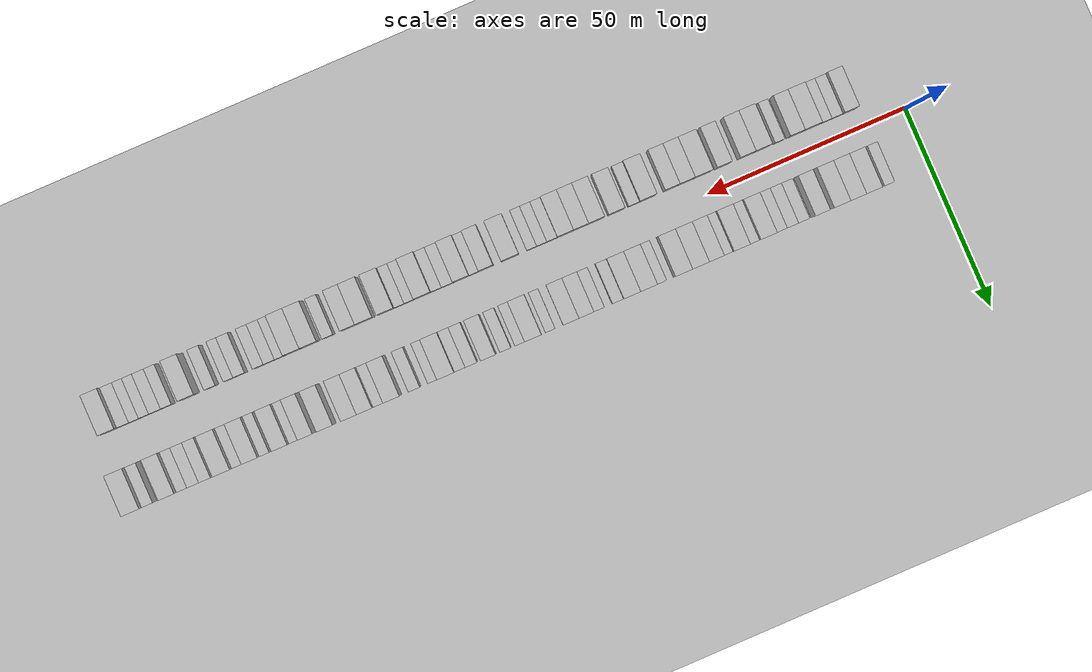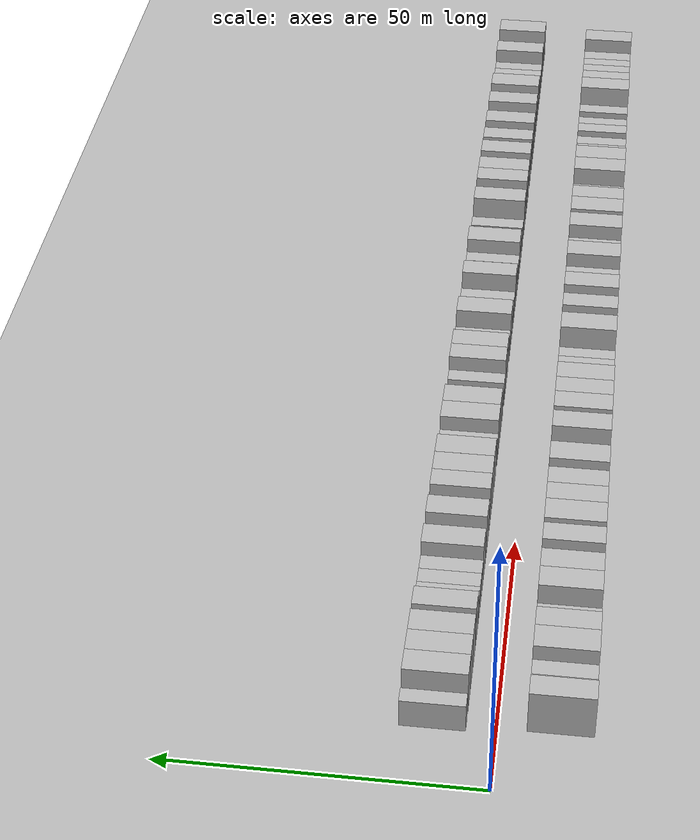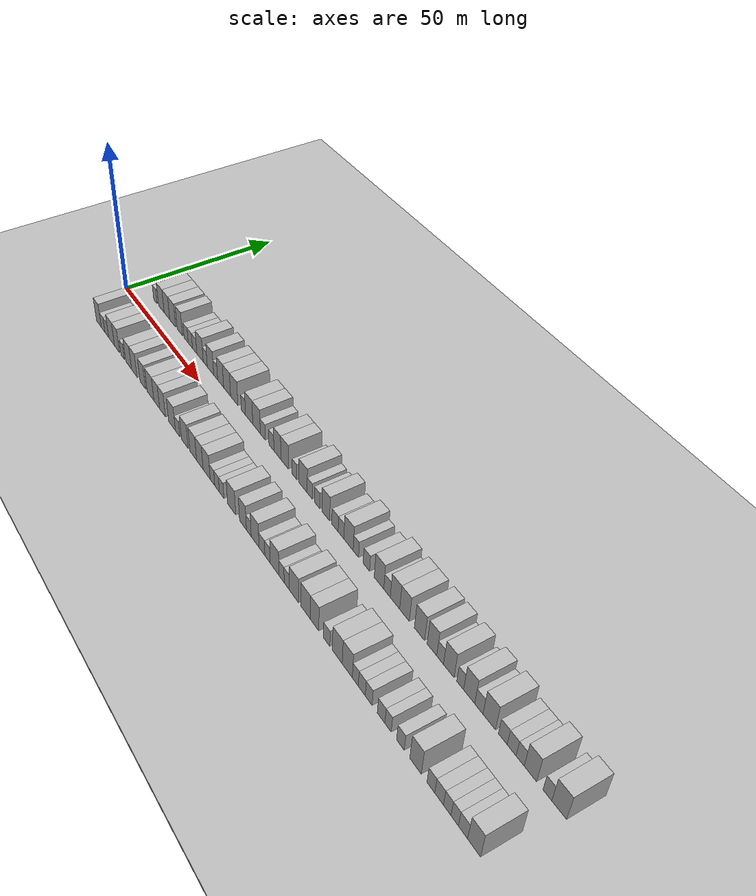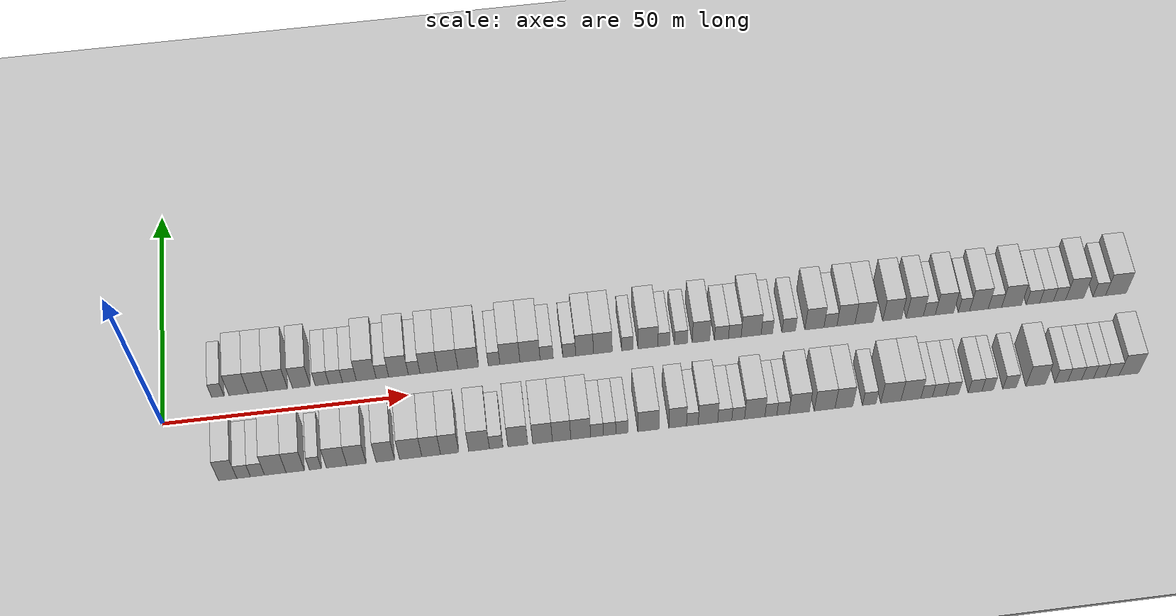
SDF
<?xml version="1.0" encoding="utf-8"?>

<sdf version="1.6">

   <world name="default">

      <gui fullscreen="0">

         <camera name="user_camera">

            <pose>-15 0 4.57585 0 0 0</pose>

            <view_controller>orbit</view_controller>

         </camera>

      </gui>

      <scene>

         <sky>

           <clouds>

             <speed>12</speed>

           </clouds>

         </sky>

         <ambient>0.4 0.4 0.4 1</ambient>

         <background>0.7 0.7 0.7 1</background>

         <shadows>1</shadows>

      </scene>

      <gravity>0 0 -9.8066</gravity>

      <magnetic_field>6e-06 2.3e-05 -4.2e-05</magnetic_field>

      <physics default="0" name="default_physics" type="ode">

         <ode>

            <solver>

               <type>quick</type>

               <iters>10</iters>

               <sor>1.0</sor>

               <use_dynamic_moi_rescaling>0</use_dynamic_moi_rescaling>

            </solver>

            <constraints>

               <cfm>0</cfm>

               <erp>0.2</erp>

               <contact_max_correcting_vel>100</contact_max_correcting_vel>

               <contact_surface_layer>0.001</contact_surface_layer>

            </constraints>

         </ode>

         <max_step_size>0.004</max_step_size>

         <real_time_factor>1</real_time_factor>

         <real_time_update_rate>250</real_time_update_rate>

      </physics>

      <light name="sun" type="directional">

         <cast_shadows>1</cast_shadows>

         <pose>0 0 10 0 0 0</pose>

         <diffuse>0.8 0.8 0.8 1</diffuse>

         <specular>0.2 0.2 0.2 1</specular>

         <attenuation>

            <range>1000</range>

            <constant>0.9</constant>

            <linear>0.01</linear>

            <quadratic>0.001</quadratic>

         </attenuation>

         <direction>-0.5 0.1 -0.9</direction>

      </light>

      <include>

         <name>ground_plane_1</name>

         <uri>model://HANNAS_ground_plane</uri>

         <pose>0 0 0  0 0 0</pose>

      </include>

      <include>

         <name>ground_plane_2</name>

         <uri>model://HANNAS_ground_plane</uri>

         <pose>100 0 0  0 0 0</pose>

      </include>

      <model name="building_1">

         <static>1</static>

         <pose frame="">11.2591 9.5000 0 0.000000 0.000000 1.570796</pose>

         <link name="link">

            <pose frame="">0 0 3.00 0 0 0</pose>

            <collision name="collision">

               <geometry>

                  <box>

                     <size>10.0000 2.5181 6.0000</size>

                  </box>

               </geometry>

               <max_contacts>10</max_contacts>

               <surface>

                  <contact>

                     <ode/>

                  </contact>

                  <bounce/>

                  <friction>

                     <torsional>

                        <ode/>

                     </torsional>

                     <ode/>

                  </friction>

               </surface>

            </collision>

            <visual name="visual">

               <cast_shadows>0</cast_shadows>

               <geometry>

                  <box>

                     <size>10.0000 2.5181 6.0000</size>

                  </box>

               </geometry>

               <material>

                  <script>

                     <uri>model://HANNAS_wall/materials/scripts</uri>

                     <uri>model://HANNAS_wall/materials/textures</uri>

                     <name>vrc/HANNAS_wall</name>

                  </script>

               </material>

            </visual>

            <self_collide>0</self_collide>

            <enable_wind>0</enable_wind>

            <kinematic>0</kinematic>

         </link>

      </model>

      <model name="building_2">

         <static>1</static>

         <pose frame="">15.4952 9.5000 0 0.000000 0.000000 1.570796</pose>

         <link name="link">

            <pose frame="">0 0 4.50 0 0 0</pose>

            <collision name="collision">

               <geometry>

                  <box>

                     <size>10.0000 3.9541 9.0000</size>

                  </box>

               </geometry>

               <max_contacts>10</max_contacts>

               <surface>

                  <contact>

                     <ode/>

                  </contact>

                  <bounce/>

                  <friction>

                     <torsional>

                        <ode/>

                     </torsional>

                     <ode/>

                  </friction>

               </surface>

            </collision>

            <visual name="visual">

               <cast_shadows>0</cast_shadows>

               <geometry>

                  <box>

                     <size>10.0000 3.9541 9.0000</size>

                  </box>

               </geometry>

               <material>

                  <script>

                     <uri>model://HANNAS_wall/materials/scripts</uri>

                     <uri>model://HANNAS_wall/materials/textures</uri>

                     <name>vrc/HANNAS_wall</name>

                  </script>

               </material>

            </visual>

            <self_collide>0</self_collide>

            <enable_wind>0</enable_wind>

            <kinematic>0</kinematic>

         </link>

      </model>

      <model name="building_3">

         <static>1</static>

         <pose frame="">19.4409 9.5000 0 0.000000 0.000000 1.570796</pose>

         <link name="link">

            <pose frame="">0 0 4.50 0 0 0</pose>

            <collision name="collision">

               <geometry>

                  <box>

                     <size>10.0000 3.9372 9.0000</size>

                  </box>

               </geometry>

               <max_contacts>10</max_contacts>

               <surface>

                  <contact>

                     <ode/>

                  </contact>

                  <bounce/>

                  <friction>

                     <torsional>

                        <ode/>

                     </torsional>

                     <ode/>

                  </friction>

               </surface>

            </collision>

            <visual name="visual">

               <cast_shadows>0</cast_shadows>

               <geometry>

                  <box>

                     <size>10.0000 3.9372 9.0000</size>

                  </box>

               </geometry>

               <material>

                  <script>

                     <uri>model://HANNAS_wall/materials/scripts</uri>

                     <uri>model://HANNAS_wall/materials/textures</uri>

                     <name>vrc/HANNAS_wall</name>

                  </script>

               </material>

            </visual>

            <self_collide>0</self_collide>

            <enable_wind>0</enable_wind>

            <kinematic>0</kinematic>

         </link>

      </model>

      <model name="building_4">

         <static>1</static>

         <pose frame="">23.4566 9.5000 0 0.000000 0.000000 1.570796</pose>

         <link name="link">

            <pose frame="">0 0 4.50 0 0 0</pose>

            <collision name="collision">

               <geometry>

                  <box>

                     <size>10.0000 4.0942 9.0000</size>

                  </box>

               </geometry>

               <max_contacts>10</max_contacts>

               <surface>

                  <contact>

                     <ode/>

                  </contact>

                  <bounce/>

                  <friction>

                     <torsional>

                        <ode/>

                     </torsional>

                     <ode/>

                  </friction>

               </surface>

            </collision>

            <visual name="visual">

               <cast_shadows>0</cast_shadows>

               <geometry>

                  <box>

                     <size>10.0000 4.0942 9.0000</size>

                  </box>

               </geometry>

               <material>

                  <script>

                     <uri>model://HANNAS_wall/materials/scripts</uri>

                     <uri>model://HANNAS_wall/materials/textures</uri>

                     <name>vrc/HANNAS_wall</name>

                  </script>

               </material>

            </visual>

            <self_collide>0</self_collide>

            <enable_wind>0</enable_wind>

            <kinematic>0</kinematic>

         </link>

      </model>

      <model name="building_5">

         <static>1</static>

         <pose frame="">28.3502 9.5000 0 0.000000 0.000000 1.570796</pose>

         <link name="link">

            <pose frame="">0 0 4.50 0 0 0</pose>

            <collision name="collision">

               <geometry>

                  <box>

                     <size>10.0000 3.6929 9.0000</size>

                  </box>

               </geometry>

               <max_contacts>10</max_contacts>

               <surface>

                  <contact>

                     <ode/>

                  </contact>

                  <bounce/>

                  <friction>

                     <torsional>

                        <ode/>

                     </torsional>

                     <ode/>

                  </friction>

               </surface>

            </collision>

            <visual name="visual">

               <cast_shadows>0</cast_shadows>

               <geometry>

                  <box>

                     <size>10.0000 3.6929 9.0000</size>

                  </box>

               </geometry>

               <material>

                  <script>

                     <uri>model://HANNAS_wall/materials/scripts</uri>

                     <uri>model://HANNAS_wall/materials/textures</uri>

                     <name>vrc/HANNAS_wall</name>

                  </script>

               </material>

            </visual>

            <self_collide>0</self_collide>

            <enable_wind>0</enable_wind>

            <kinematic>0</kinematic>

         </link>

      </model>

      <model name="building_6">

         <static>1</static>

         <pose frame="">32.5860 9.5000 0 0.000000 0.000000 1.570796</pose>

         <link name="link">

            <pose frame="">0 0 3.00 0 0 0</pose>

            <collision name="collision">

               <geometry>

                  <box>

                     <size>10.0000 2.7786 6.0000</size>

                  </box>

               </geometry>

               <max_contacts>10</max_contacts>

               <surface>

                  <contact>

                     <ode/>

                  </contact>

                  <bounce/>

                  <friction>

                     <torsional>

                        <ode/>

                     </torsional>

                     <ode/>

                  </friction>

               </surface>

            </collision>

            <visual name="visual">

               <cast_shadows>0</cast_shadows>

               <geometry>

                  <box>

                     <size>10.0000 2.7786 6.0000</size>

                  </box>

               </geometry>

               <material>

                  <script>

                     <uri>model://HANNAS_wall/materials/scripts</uri>

                     <uri>model://HANNAS_wall/materials/textures</uri>

                     <name>vrc/HANNAS_wall</name>

                  </script>

               </material>

            </visual>

            <self_collide>0</self_collide>

            <enable_wind>0</enable_wind>

            <kinematic>0</kinematic>

         </link>

      </model>

      <model name="building_7">

         <static>1</static>

         <pose frame="">35.3930 9.5000 0 0.000000 0.000000 1.570796</pose>

         <link name="link">

            <pose frame="">0 0 3.00 0 0 0</pose>

            <collision name="collision">

               <geometry>

                  <box>

                     <size>10.0000 2.8354 6.0000</size>

                  </box>

               </geometry>

               <max_contacts>10</max_contacts>

               <surface>

                  <contact>

                     <ode/>

                  </contact>

                  <bounce/>

                  <friction>

                     <torsional>

                        <ode/>

                     </torsional>

                     <ode/>

                  </friction>

               </surface>

            </collision>

            <visual name="visual">

               <cast_shadows>0</cast_shadows>

               <geometry>

                  <box>

                     <size>10.0000 2.8354 6.0000</size>

                  </box>

               </geometry>

               <material>

                  <script>

                     <uri>model://HANNAS_wall/materials/scripts</uri>

                     <uri>model://HANNAS_wall/materials/textures</uri>

                     <name>vrc/HANNAS_wall</name>

                  </script>

               </material>

            </visual>

            <self_collide>0</self_collide>

            <enable_wind>0</enable_wind>

            <kinematic>0</kinematic>

         </link>

      </model>

      <model name="building_8">

         <static>1</static>

         <pose frame="">38.2418 9.5000 0 0.000000 0.000000 1.570796</pose>

         <link name="link">

            <pose frame="">0 0 3.00 0 0 0</pose>

            <collision name="collision">

               <geometry>

                  <box>

                     <size>10.0000 2.8623 6.0000</size>

                  </box>

               </geometry>

               <max_contacts>10</max_contacts>

               <surface>

                  <contact>

                     <ode/>

                  </contact>

                  <bounce/>

                  <friction>

                     <torsional>

                        <ode/>

                     </torsional>

                     <ode/>

                  </friction>

               </surface>

            </collision>

            <visual name="visual">

               <cast_shadows>0</cast_shadows>

               <geometry>

                  <box>

                     <size>10.0000 2.8623 6.0000</size>

                  </box>

               </geometry>

               <material>

                  <script>

                     <uri>model://HANNAS_wall/materials/scripts</uri>

                     <uri>model://HANNAS_wall/materials/textures</uri>

                     <name>vrc/HANNAS_wall</name>

                  </script>

               </material>

            </visual>

            <self_collide>0</self_collide>

            <enable_wind>0</enable_wind>

            <kinematic>0</kinematic>

         </link>

      </model>

      <model name="building_9">

         <static>1</static>

         <pose frame="">41.7074 9.5000 0 0.000000 0.000000 1.570796</pose>

         <link name="link">

            <pose frame="">0 0 4.50 0 0 0</pose>

            <collision name="collision">

               <geometry>

                  <box>

                     <size>10.0000 4.0688 9.0000</size>

                  </box>

               </geometry>

               <max_contacts>10</max_contacts>

               <surface>

                  <contact>

                     <ode/>

                  </contact>

                  <bounce/>

                  <friction>

                     <torsional>

                        <ode/>

                     </torsional>

                     <ode/>

                  </friction>

               </surface>

            </collision>

            <visual name="visual">

               <cast_shadows>0</cast_shadows>

               <geometry>

                  <box>

                     <size>10.0000 4.0688 9.0000</size>

                  </box>

               </geometry>

               <material>

                  <script>

                     <uri>model://HANNAS_wall/materials/scripts</uri>

                     <uri>model://HANNAS_wall/materials/textures</uri>

                     <name>vrc/HANNAS_wall</name>

                  </script>

               </material>

            </visual>

            <self_collide>0</self_collide>

            <enable_wind>0</enable_wind>

            <kinematic>0</kinematic>

         </link>

      </model>

      <model name="building_10">

         <static>1</static>

         <pose frame="">45.0403 9.5000 0 0.000000 0.000000 1.570796</pose>

         <link name="link">

            <pose frame="">0 0 3.00 0 0 0</pose>

            <collision name="collision">

               <geometry>

                  <box>

                     <size>10.0000 2.5971 6.0000</size>

                  </box>

               </geometry>

               <max_contacts>10</max_contacts>

               <surface>

                  <contact>

                     <ode/>

                  </contact>

                  <bounce/>

                  <friction>

                     <torsional>

                        <ode/>

                     </torsional>

                     <ode/>

                  </friction>

               </surface>

            </collision>

            <visual name="visual">

               <cast_shadows>0</cast_shadows>

               <geometry>

                  <box>

                     <size>10.0000 2.5971 6.0000</size>

                  </box>

               </geometry>

               <material>

                  <script>

                     <uri>model://HANNAS_wall/materials/scripts</uri>

                     <uri>model://HANNAS_wall/materials/textures</uri>

                     <name>vrc/HANNAS_wall</name>

                  </script>

               </material>

            </visual>

            <self_collide>0</self_collide>

            <enable_wind>0</enable_wind>

            <kinematic>0</kinematic>

         </link>

      </model>

      <model name="building_11">

         <static>1</static>

         <pose frame="">48.3593 9.5000 0 0.000000 0.000000 1.570796</pose>

         <link name="link">

            <pose frame="">0 0 4.50 0 0 0</pose>

            <collision name="collision">

               <geometry>

                  <box>

                     <size>10.0000 4.0409 9.0000</size>

                  </box>

               </geometry>

               <max_contacts>10</max_contacts>

               <surface>

                  <contact>

                     <ode/>

                  </contact>

                  <bounce/>

                  <friction>

                     <torsional>

                        <ode/>

                     </torsional>

                     <ode/>

                  </friction>

               </surface>

            </collision>

            <visual name="visual">

               <cast_shadows>0</cast_shadows>

               <geometry>

                  <box>

                     <size>10.0000 4.0409 9.0000</size>

                  </box>

               </geometry>

               <material>

                  <script>

                     <uri>model://HANNAS_wall/materials/scripts</uri>

                     <uri>model://HANNAS_wall/materials/textures</uri>

                     <name>vrc/HANNAS_wall</name>

                  </script>

               </material>

            </visual>

            <self_collide>0</self_collide>

            <enable_wind>0</enable_wind>

            <kinematic>0</kinematic>

         </link>

      </model>

      <model name="building_12">

         <static>1</static>

         <pose frame="">51.5894 9.5000 0 0.000000 0.000000 1.570796</pose>

         <link name="link">

            <pose frame="">0 0 3.00 0 0 0</pose>

            <collision name="collision">

               <geometry>

                  <box>

                     <size>10.0000 2.4194 6.0000</size>

                  </box>

               </geometry>

               <max_contacts>10</max_contacts>

               <surface>

                  <contact>

                     <ode/>

                  </contact>

                  <bounce/>

                  <friction>

                     <torsional>

                        <ode/>

                     </torsional>

                     <ode/>

                  </friction>

               </surface>

            </collision>

            <visual name="visual">

               <cast_shadows>0</cast_shadows>

               <geometry>

                  <box>

                     <size>10.0000 2.4194 6.0000</size>

                  </box>

               </geometry>

               <material>

                  <script>

                     <uri>model://HANNAS_wall/materials/scripts</uri>

                     <uri>model://HANNAS_wall/materials/textures</uri>

                     <name>vrc/HANNAS_wall</name>

                  </script>

               </material>

            </visual>

            <self_collide>0</self_collide>

            <enable_wind>0</enable_wind>

            <kinematic>0</kinematic>

         </link>

      </model>

      <model name="building_13">

         <static>1</static>

         <pose frame="">54.6429 9.5000 0 0.000000 0.000000 1.570796</pose>

         <link name="link">

            <pose frame="">0 0 4.50 0 0 0</pose>

            <collision name="collision">

               <geometry>

                  <box>

                     <size>10.0000 3.6875 9.0000</size>

                  </box>

               </geometry>

               <max_contacts>10</max_contacts>

               <surface>

                  <contact>

                     <ode/>

                  </contact>

                  <bounce/>

                  <friction>

                     <torsional>

                        <ode/>

                     </torsional>

                     <ode/>

                  </friction>

               </surface>

            </collision>

            <visual name="visual">

               <cast_shadows>0</cast_shadows>

               <geometry>

                  <box>

                     <size>10.0000 3.6875 9.0000</size>

                  </box>

               </geometry>

               <material>

                  <script>

                     <uri>model://HANNAS_wall/materials/scripts</uri>

                     <uri>model://HANNAS_wall/materials/textures</uri>

                     <name>vrc/HANNAS_wall</name>

                  </script>

               </material>

            </visual>

            <self_collide>0</self_collide>

            <enable_wind>0</enable_wind>

            <kinematic>0</kinematic>

         </link>

      </model>

      <model name="building_14">

         <static>1</static>

         <pose frame="">58.5699 9.5000 0 0.000000 0.000000 1.570796</pose>

         <link name="link">

            <pose frame="">0 0 4.50 0 0 0</pose>

            <collision name="collision">

               <geometry>

                  <box>

                     <size>10.0000 4.1665 9.0000</size>

                  </box>

               </geometry>

               <max_contacts>10</max_contacts>

               <surface>

                  <contact>

                     <ode/>

                  </contact>

                  <bounce/>

                  <friction>

                     <torsional>

                        <ode/>

                     </torsional>

                     <ode/>

                  </friction>

               </surface>

            </collision>

            <visual name="visual">

               <cast_shadows>0</cast_shadows>

               <geometry>

                  <box>

                     <size>10.0000 4.1665 9.0000</size>

                  </box>

               </geometry>

               <material>

                  <script>

                     <uri>model://HANNAS_wall/materials/scripts</uri>

                     <uri>model://HANNAS_wall/materials/textures</uri>

                     <name>vrc/HANNAS_wall</name>

                  </script>

               </material>

            </visual>

            <self_collide>0</self_collide>

            <enable_wind>0</enable_wind>

            <kinematic>0</kinematic>

         </link>

      </model>

      <model name="building_15">

         <static>1</static>

         <pose frame="">62.7989 9.5000 0 0.000000 0.000000 1.570796</pose>

         <link name="link">

            <pose frame="">0 0 4.50 0 0 0</pose>

            <collision name="collision">

               <geometry>

                  <box>

                     <size>10.0000 4.2914 9.0000</size>

                  </box>

               </geometry>

               <max_contacts>10</max_contacts>

               <surface>

                  <contact>

                     <ode/>

                  </contact>

                  <bounce/>

                  <friction>

                     <torsional>

                        <ode/>

                     </torsional>

                     <ode/>

                  </friction>

               </surface>

            </collision>

            <visual name="visual">

               <cast_shadows>0</cast_shadows>

               <geometry>

                  <box>

                     <size>10.0000 4.2914 9.0000</size>

                  </box>

               </geometry>

               <material>

                  <script>

                     <uri>model://HANNAS_wall/materials/scripts</uri>

                     <uri>model://HANNAS_wall/materials/textures</uri>

                     <name>vrc/HANNAS_wall</name>

                  </script>

               </material>

            </visual>

            <self_collide>0</self_collide>

            <enable_wind>0</enable_wind>

            <kinematic>0</kinematic>

         </link>

      </model>

      <model name="building_16">

         <static>1</static>

         <pose frame="">68.1604 9.5000 0 0.000000 0.000000 1.570796</pose>

         <link name="link">

            <pose frame="">0 0 3.00 0 0 0</pose>

            <collision name="collision">

               <geometry>

                  <box>

                     <size>10.0000 2.4318 6.0000</size>

                  </box>

               </geometry>

               <max_contacts>10</max_contacts>

               <surface>

                  <contact>

                     <ode/>

                  </contact>

                  <bounce/>

                  <friction>

                     <torsional>

                        <ode/>

                     </torsional>

                     <ode/>

                  </friction>

               </surface>

            </collision>

            <visual name="visual">

               <cast_shadows>0</cast_shadows>

               <geometry>

                  <box>

                     <size>10.0000 2.4318 6.0000</size>

                  </box>

               </geometry>

               <material>

                  <script>

                     <uri>model://HANNAS_wall/materials/scripts</uri>

                     <uri>model://HANNAS_wall/materials/textures</uri>

                     <name>vrc/HANNAS_wall</name>

                  </script>

               </material>

            </visual>

            <self_collide>0</self_collide>

            <enable_wind>0</enable_wind>

            <kinematic>0</kinematic>

         </link>

      </model>

      <model name="building_17">

         <static>1</static>

         <pose frame="">71.4550 9.5000 0 0.000000 0.000000 1.570796</pose>

         <link name="link">

            <pose frame="">0 0 4.50 0 0 0</pose>

            <collision name="collision">

               <geometry>

                  <box>

                     <size>10.0000 4.1574 9.0000</size>

                  </box>

               </geometry>

               <max_contacts>10</max_contacts>

               <surface>

                  <contact>

                     <ode/>

                  </contact>

                  <bounce/>

                  <friction>

                     <torsional>

                        <ode/>

                     </torsional>

                     <ode/>

                  </friction>

               </surface>

            </collision>

            <visual name="visual">

               <cast_shadows>0</cast_shadows>

               <geometry>

                  <box>

                     <size>10.0000 4.1574 9.0000</size>

                  </box>

               </geometry>

               <material>

                  <script>

                     <uri>model://HANNAS_wall/materials/scripts</uri>

                     <uri>model://HANNAS_wall/materials/textures</uri>

                     <name>vrc/HANNAS_wall</name>

                  </script>

               </material>

            </visual>

            <self_collide>0</self_collide>

            <enable_wind>0</enable_wind>

            <kinematic>0</kinematic>

         </link>

      </model>

      <model name="building_18">

         <static>1</static>

         <pose frame="">75.6295 9.5000 0 0.000000 0.000000 1.570796</pose>

         <link name="link">

            <pose frame="">0 0 4.50 0 0 0</pose>

            <collision name="collision">

               <geometry>

                  <box>

                     <size>10.0000 4.1917 9.0000</size>

                  </box>

               </geometry>

               <max_contacts>10</max_contacts>

               <surface>

                  <contact>

                     <ode/>

                  </contact>

                  <bounce/>

                  <friction>

                     <torsional>

                        <ode/>

                     </torsional>

                     <ode/>

                  </friction>

               </surface>

            </collision>

            <visual name="visual">

               <cast_shadows>0</cast_shadows>

               <geometry>

                  <box>

                     <size>10.0000 4.1917 9.0000</size>

                  </box>

               </geometry>

               <material>

                  <script>

                     <uri>model://HANNAS_wall/materials/scripts</uri>

                     <uri>model://HANNAS_wall/materials/textures</uri>

                     <name>vrc/HANNAS_wall</name>

                  </script>

               </material>

            </visual>

            <self_collide>0</self_collide>

            <enable_wind>0</enable_wind>

            <kinematic>0</kinematic>

         </link>

      </model>

      <model name="building_19">

         <static>1</static>

         <pose frame="">79.0983 9.5000 0 0.000000 0.000000 1.570796</pose>

         <link name="link">

            <pose frame="">0 0 3.00 0 0 0</pose>

            <collision name="collision">

               <geometry>

                  <box>

                     <size>10.0000 2.7459 6.0000</size>

                  </box>

               </geometry>

               <max_contacts>10</max_contacts>

               <surface>

                  <contact>

                     <ode/>

                  </contact>

                  <bounce/>

                  <friction>

                     <torsional>

                        <ode/>

                     </torsional>

                     <ode/>

                  </friction>

               </surface>

            </collision>

            <visual name="visual">

               <cast_shadows>0</cast_shadows>

               <geometry>

                  <box>

                     <size>10.0000 2.7459 6.0000</size>

                  </box>

               </geometry>

               <material>

                  <script>

                     <uri>model://HANNAS_wall/materials/scripts</uri>

                     <uri>model://HANNAS_wall/materials/textures</uri>

                     <name>vrc/HANNAS_wall</name>

                  </script>

               </material>

            </visual>

            <self_collide>0</self_collide>

            <enable_wind>0</enable_wind>

            <kinematic>0</kinematic>

         </link>

      </model>

      <model name="building_20">

         <static>1</static>

         <pose frame="">83.8172 9.5000 0 0.000000 0.000000 1.570796</pose>

         <link name="link">

            <pose frame="">0 0 3.00 0 0 0</pose>

            <collision name="collision">

               <geometry>

                  <box>

                     <size>10.0000 2.6920 6.0000</size>

                  </box>

               </geometry>

               <max_contacts>10</max_contacts>

               <surface>

                  <contact>

                     <ode/>

                  </contact>

                  <bounce/>

                  <friction>

                     <torsional>

                        <ode/>

                     </torsional>

                     <ode/>

                  </friction>

               </surface>

            </collision>

            <visual name="visual">

               <cast_shadows>0</cast_shadows>

               <geometry>

                  <box>

                     <size>10.0000 2.6920 6.0000</size>

                  </box>

               </geometry>

               <material>

                  <script>

                     <uri>model://HANNAS_wall/materials/scripts</uri>

                     <uri>model://HANNAS_wall/materials/textures</uri>

                     <name>vrc/HANNAS_wall</name>

                  </script>

               </material>

            </visual>

            <self_collide>0</self_collide>

            <enable_wind>0</enable_wind>

            <kinematic>0</kinematic>

         </link>

      </model>

      <model name="building_21">

         <static>1</static>

         <pose frame="">87.0149 9.5000 0 0.000000 0.000000 1.570796</pose>

         <link name="link">

            <pose frame="">0 0 4.50 0 0 0</pose>

            <collision name="collision">

               <geometry>

                  <box>

                     <size>10.0000 3.7034 9.0000</size>

                  </box>

               </geometry>

               <max_contacts>10</max_contacts>

               <surface>

                  <contact>

                     <ode/>

                  </contact>

                  <bounce/>

                  <friction>

                     <torsional>

                        <ode/>

                     </torsional>

                     <ode/>

                  </friction>

               </surface>

            </collision>

            <visual name="visual">

               <cast_shadows>0</cast_shadows>

               <geometry>

                  <box>

                     <size>10.0000 3.7034 9.0000</size>

                  </box>

               </geometry>

               <material>

                  <script>

                     <uri>model://HANNAS_wall/materials/scripts</uri>

                     <uri>model://HANNAS_wall/materials/textures</uri>

                     <name>vrc/HANNAS_wall</name>

                  </script>

               </material>

            </visual>

            <self_collide>0</self_collide>

            <enable_wind>0</enable_wind>

            <kinematic>0</kinematic>

         </link>

      </model>

      <model name="building_22">

         <static>1</static>

         <pose frame="">90.8317 9.5000 0 0.000000 0.000000 1.570796</pose>

         <link name="link">

            <pose frame="">0 0 4.50 0 0 0</pose>

            <collision name="collision">

               <geometry>

                  <box>

                     <size>10.0000 3.9303 9.0000</size>

                  </box>

               </geometry>

               <max_contacts>10</max_contacts>

               <surface>

                  <contact>

                     <ode/>

                  </contact>

                  <bounce/>

                  <friction>

                     <torsional>

                        <ode/>

                     </torsional>

                     <ode/>

                  </friction>

               </surface>

            </collision>

            <visual name="visual">

               <cast_shadows>0</cast_shadows>

               <geometry>

                  <box>

                     <size>10.0000 3.9303 9.0000</size>

                  </box>

               </geometry>

               <material>

                  <script>

                     <uri>model://HANNAS_wall/materials/scripts</uri>

                     <uri>model://HANNAS_wall/materials/textures</uri>

                     <name>vrc/HANNAS_wall</name>

                  </script>

               </material>

            </visual>

            <self_collide>0</self_collide>

            <enable_wind>0</enable_wind>

            <kinematic>0</kinematic>

         </link>

      </model>

      <model name="building_23">

         <static>1</static>

         <pose frame="">96.0097 9.5000 0 0.000000 0.000000 1.570796</pose>

         <link name="link">

            <pose frame="">0 0 3.00 0 0 0</pose>

            <collision name="collision">

               <geometry>

                  <box>

                     <size>10.0000 2.4257 6.0000</size>

                  </box>

               </geometry>

               <max_contacts>10</max_contacts>

               <surface>

                  <contact>

                     <ode/>

                  </contact>

                  <bounce/>

                  <friction>

                     <torsional>

                        <ode/>

                     </torsional>

                     <ode/>

                  </friction>

               </surface>

            </collision>

            <visual name="visual">

               <cast_shadows>0</cast_shadows>

               <geometry>

                  <box>

                     <size>10.0000 2.4257 6.0000</size>

                  </box>

               </geometry>

               <material>

                  <script>

                     <uri>model://HANNAS_wall/materials/scripts</uri>

                     <uri>model://HANNAS_wall/materials/textures</uri>

                     <name>vrc/HANNAS_wall</name>

                  </script>

               </material>

            </visual>

            <self_collide>0</self_collide>

            <enable_wind>0</enable_wind>

            <kinematic>0</kinematic>

         </link>

      </model>

      <model name="building_24">

         <static>1</static>

         <pose frame="">100.3066 9.5000 0 0.000000 0.000000 1.570796</pose>

         <link name="link">

            <pose frame="">0 0 4.50 0 0 0</pose>

            <collision name="collision">

               <geometry>

                  <box>

                     <size>10.0000 4.1679 9.0000</size>

                  </box>

               </geometry>

               <max_contacts>10</max_contacts>

               <surface>

                  <contact>

                     <ode/>

                  </contact>

                  <bounce/>

                  <friction>

                     <torsional>

                        <ode/>

                     </torsional>

                     <ode/>

                  </friction>

               </surface>

            </collision>

            <visual name="visual">

               <cast_shadows>0</cast_shadows>

               <geometry>

                  <box>

                     <size>10.0000 4.1679 9.0000</size>

                  </box>

               </geometry>

               <material>

                  <script>

                     <uri>model://HANNAS_wall/materials/scripts</uri>

                     <uri>model://HANNAS_wall/materials/textures</uri>

                     <name>vrc/HANNAS_wall</name>

                  </script>

               </material>

            </visual>

            <self_collide>0</self_collide>

            <enable_wind>0</enable_wind>

            <kinematic>0</kinematic>

         </link>

      </model>

      <model name="building_25">

         <static>1</static>

         <pose frame="">103.6202 9.5000 0 0.000000 0.000000 1.570796</pose>

         <link name="link">

            <pose frame="">0 0 3.00 0 0 0</pose>

            <collision name="collision">

               <geometry>

                  <box>

                     <size>10.0000 2.4592 6.0000</size>

                  </box>

               </geometry>

               <max_contacts>10</max_contacts>

               <surface>

                  <contact>

                     <ode/>

                  </contact>

                  <bounce/>

                  <friction>

                     <torsional>

                        <ode/>

                     </torsional>

                     <ode/>

                  </friction>

               </surface>

            </collision>

            <visual name="visual">

               <cast_shadows>0</cast_shadows>

               <geometry>

                  <box>

                     <size>10.0000 2.4592 6.0000</size>

                  </box>

               </geometry>

               <material>

                  <script>

                     <uri>model://HANNAS_wall/materials/scripts</uri>

                     <uri>model://HANNAS_wall/materials/textures</uri>

                     <name>vrc/HANNAS_wall</name>

                  </script>

               </material>

            </visual>

            <self_collide>0</self_collide>

            <enable_wind>0</enable_wind>

            <kinematic>0</kinematic>

         </link>

      </model>

      <model name="building_26">

         <static>1</static>

         <pose frame="">107.2216 9.5000 0 0.000000 0.000000 1.570796</pose>

         <link name="link">

            <pose frame="">0 0 3.00 0 0 0</pose>

            <collision name="collision">

               <geometry>

                  <box>

                     <size>10.0000 2.7436 6.0000</size>

                  </box>

               </geometry>

               <max_contacts>10</max_contacts>

               <surface>

                  <contact>

                     <ode/>

                  </contact>

                  <bounce/>

                  <friction>

                     <torsional>

                        <ode/>

                     </torsional>

                     <ode/>

                  </friction>

               </surface>

            </collision>

            <visual name="visual">

               <cast_shadows>0</cast_shadows>

               <geometry>

                  <box>

                     <size>10.0000 2.7436 6.0000</size>

                  </box>

               </geometry>

               <material>

                  <script>

                     <uri>model://HANNAS_wall/materials/scripts</uri>

                     <uri>model://HANNAS_wall/materials/textures</uri>

                     <name>vrc/HANNAS_wall</name>

                  </script>

               </material>

            </visual>

            <self_collide>0</self_collide>

            <enable_wind>0</enable_wind>

            <kinematic>0</kinematic>

         </link>

      </model>

      <model name="building_27">

         <static>1</static>

         <pose frame="">111.4386 9.5000 0 0.000000 0.000000 1.570796</pose>

         <link name="link">

            <pose frame="">0 0 4.50 0 0 0</pose>

            <collision name="collision">

               <geometry>

                  <box>

                     <size>10.0000 3.6904 9.0000</size>

                  </box>

               </geometry>

               <max_contacts>10</max_contacts>

               <surface>

                  <contact>

                     <ode/>

                  </contact>

                  <bounce/>

                  <friction>

                     <torsional>

                        <ode/>

                     </torsional>

                     <ode/>

                  </friction>

               </surface>

            </collision>

            <visual name="visual">

               <cast_shadows>0</cast_shadows>

               <geometry>

                  <box>

                     <size>10.0000 3.6904 9.0000</size>

                  </box>

               </geometry>

               <material>

                  <script>

                     <uri>model://HANNAS_wall/materials/scripts</uri>

                     <uri>model://HANNAS_wall/materials/textures</uri>

                     <name>vrc/HANNAS_wall</name>

                  </script>

               </material>

            </visual>

            <self_collide>0</self_collide>

            <enable_wind>0</enable_wind>

            <kinematic>0</kinematic>

         </link>

      </model>

      <model name="building_28">

         <static>1</static>

         <pose frame="">115.7671 9.5000 0 0.000000 0.000000 1.570796</pose>

         <link name="link">

            <pose frame="">0 0 3.00 0 0 0</pose>

            <collision name="collision">

               <geometry>

                  <box>

                     <size>10.0000 2.9667 6.0000</size>

                  </box>

               </geometry>

               <max_contacts>10</max_contacts>

               <surface>

                  <contact>

                     <ode/>

                  </contact>

                  <bounce/>

                  <friction>

                     <torsional>

                        <ode/>

                     </torsional>

                     <ode/>

                  </friction>

               </surface>

            </collision>

            <visual name="visual">

               <cast_shadows>0</cast_shadows>

               <geometry>

                  <box>

                     <size>10.0000 2.9667 6.0000</size>

                  </box>

               </geometry>

               <material>

                  <script>

                     <uri>model://HANNAS_wall/materials/scripts</uri>

                     <uri>model://HANNAS_wall/materials/textures</uri>

                     <name>vrc/HANNAS_wall</name>

                  </script>

               </material>

            </visual>

            <self_collide>0</self_collide>

            <enable_wind>0</enable_wind>

            <kinematic>0</kinematic>

         </link>

      </model>

      <model name="building_29">

         <static>1</static>

         <pose frame="">118.5876 9.5000 0 0.000000 0.000000 1.570796</pose>

         <link name="link">

            <pose frame="">0 0 3.00 0 0 0</pose>

            <collision name="collision">

               <geometry>

                  <box>

                     <size>10.0000 2.6743 6.0000</size>

                  </box>

               </geometry>

               <max_contacts>10</max_contacts>

               <surface>

                  <contact>

                     <ode/>

                  </contact>

                  <bounce/>

                  <friction>

                     <torsional>

                        <ode/>

                     </torsional>

                     <ode/>

                  </friction>

               </surface>

            </collision>

            <visual name="visual">

               <cast_shadows>0</cast_shadows>

               <geometry>

                  <box>

                     <size>10.0000 2.6743 6.0000</size>

                  </box>

               </geometry>

               <material>

                  <script>

                     <uri>model://HANNAS_wall/materials/scripts</uri>

                     <uri>model://HANNAS_wall/materials/textures</uri>

                     <name>vrc/HANNAS_wall</name>

                  </script>

               </material>

            </visual>

            <self_collide>0</self_collide>

            <enable_wind>0</enable_wind>

            <kinematic>0</kinematic>

         </link>

      </model>

      <model name="building_30">

         <static>1</static>

         <pose frame="">122.0365 9.5000 0 0.000000 0.000000 1.570796</pose>

         <link name="link">

            <pose frame="">0 0 4.50 0 0 0</pose>

            <collision name="collision">

               <geometry>

                  <box>

                     <size>10.0000 4.2235 9.0000</size>

                  </box>

               </geometry>

               <max_contacts>10</max_contacts>

               <surface>

                  <contact>

                     <ode/>

                  </contact>

                  <bounce/>

                  <friction>

                     <torsional>

                        <ode/>

                     </torsional>

                     <ode/>

                  </friction>

               </surface>

            </collision>

            <visual name="visual">

               <cast_shadows>0</cast_shadows>

               <geometry>

                  <box>

                     <size>10.0000 4.2235 9.0000</size>

                  </box>

               </geometry>

               <material>

                  <script>

                     <uri>model://HANNAS_wall/materials/scripts</uri>

                     <uri>model://HANNAS_wall/materials/textures</uri>

                     <name>vrc/HANNAS_wall</name>

                  </script>

               </material>

            </visual>

            <self_collide>0</self_collide>

            <enable_wind>0</enable_wind>

            <kinematic>0</kinematic>

         </link>

      </model>

      <model name="building_31">

         <static>1</static>

         <pose frame="">125.3655 9.5000 0 0.000000 0.000000 1.570796</pose>

         <link name="link">

            <pose frame="">0 0 3.00 0 0 0</pose>

            <collision name="collision">

               <geometry>

                  <box>

                     <size>10.0000 2.4346 6.0000</size>

                  </box>

               </geometry>

               <max_contacts>10</max_contacts>

               <surface>

                  <contact>

                     <ode/>

                  </contact>

                  <bounce/>

                  <friction>

                     <torsional>

                        <ode/>

                     </torsional>

                     <ode/>

                  </friction>

               </surface>

            </collision>

            <visual name="visual">

               <cast_shadows>0</cast_shadows>

               <geometry>

                  <box>

                     <size>10.0000 2.4346 6.0000</size>

                  </box>

               </geometry>

               <material>

                  <script>

                     <uri>model://HANNAS_wall/materials/scripts</uri>

                     <uri>model://HANNAS_wall/materials/textures</uri>

                     <name>vrc/HANNAS_wall</name>

                  </script>

               </material>

            </visual>

            <self_collide>0</self_collide>

            <enable_wind>0</enable_wind>

            <kinematic>0</kinematic>

         </link>

      </model>

      <model name="building_32">

         <static>1</static>

         <pose frame="">130.0093 9.5000 0 0.000000 0.000000 1.570796</pose>

         <link name="link">

            <pose frame="">0 0 3.00 0 0 0</pose>

            <collision name="collision">

               <geometry>

                  <box>

                     <size>10.0000 2.8530 6.0000</size>

                  </box>

               </geometry>

               <max_contacts>10</max_contacts>

               <surface>

                  <contact>

                     <ode/>

                  </contact>

                  <bounce/>

                  <friction>

                     <torsional>

                        <ode/>

                     </torsional>

                     <ode/>

                  </friction>

               </surface>

            </collision>

            <visual name="visual">

               <cast_shadows>0</cast_shadows>

               <geometry>

                  <box>

                     <size>10.0000 2.8530 6.0000</size>

                  </box>

               </geometry>

               <material>

                  <script>

                     <uri>model://HANNAS_wall/materials/scripts</uri>

                     <uri>model://HANNAS_wall/materials/textures</uri>

                     <name>vrc/HANNAS_wall</name>

                  </script>

               </material>

            </visual>

            <self_collide>0</self_collide>

            <enable_wind>0</enable_wind>

            <kinematic>0</kinematic>

         </link>

      </model>

      <model name="building_33">

         <static>1</static>

         <pose frame="">135.4613 9.5000 0 0.000000 0.000000 1.570796</pose>

         <link name="link">

            <pose frame="">0 0 4.50 0 0 0</pose>

            <collision name="collision">

               <geometry>

                  <box>

                     <size>10.0000 4.0511 9.0000</size>

                  </box>

               </geometry>

               <max_contacts>10</max_contacts>

               <surface>

                  <contact>

                     <ode/>

                  </contact>

                  <bounce/>

                  <friction>

                     <torsional>

                        <ode/>

                     </torsional>

                     <ode/>

                  </friction>

               </surface>

            </collision>

            <visual name="visual">

               <cast_shadows>0</cast_shadows>

               <geometry>

                  <box>

                     <size>10.0000 4.0511 9.0000</size>

                  </box>

               </geometry>

               <material>

                  <script>

                     <uri>model://HANNAS_wall/materials/scripts</uri>

                     <uri>model://HANNAS_wall/materials/textures</uri>

                     <name>vrc/HANNAS_wall</name>

                  </script>

               </material>

            </visual>

            <self_collide>0</self_collide>

            <enable_wind>0</enable_wind>

            <kinematic>0</kinematic>

         </link>

      </model>

      <model name="building_34">

         <static>1</static>

         <pose frame="">138.8595 9.5000 0 0.000000 0.000000 1.570796</pose>

         <link name="link">

            <pose frame="">0 0 3.00 0 0 0</pose>

            <collision name="collision">

               <geometry>

                  <box>

                     <size>10.0000 2.7453 6.0000</size>

                  </box>

               </geometry>

               <max_contacts>10</max_contacts>

               <surface>

                  <contact>

                     <ode/>

                  </contact>

                  <bounce/>

                  <friction>

                     <torsional>

                        <ode/>

                     </torsional>

                     <ode/>

                  </friction>

               </surface>

            </collision>

            <visual name="visual">

               <cast_shadows>0</cast_shadows>

               <geometry>

                  <box>

                     <size>10.0000 2.7453 6.0000</size>

                  </box>

               </geometry>

               <material>

                  <script>

                     <uri>model://HANNAS_wall/materials/scripts</uri>

                     <uri>model://HANNAS_wall/materials/textures</uri>

                     <name>vrc/HANNAS_wall</name>

                  </script>

               </material>

            </visual>

            <self_collide>0</self_collide>

            <enable_wind>0</enable_wind>

            <kinematic>0</kinematic>

         </link>

      </model>

      <model name="building_35">

         <static>1</static>

         <pose frame="">142.1615 9.5000 0 0.000000 0.000000 1.570796</pose>

         <link name="link">

            <pose frame="">0 0 4.50 0 0 0</pose>

            <collision name="collision">

               <geometry>

                  <box>

                     <size>10.0000 3.8588 9.0000</size>

                  </box>

               </geometry>

               <max_contacts>10</max_contacts>

               <surface>

                  <contact>

                     <ode/>

                  </contact>

                  <bounce/>

                  <friction>

                     <torsional>

                        <ode/>

                     </torsional>

                     <ode/>

                  </friction>

               </surface>

            </collision>

            <visual name="visual">

               <cast_shadows>0</cast_shadows>

               <geometry>

                  <box>

                     <size>10.0000 3.8588 9.0000</size>

                  </box>

               </geometry>

               <material>

                  <script>

                     <uri>model://HANNAS_wall/materials/scripts</uri>

                     <uri>model://HANNAS_wall/materials/textures</uri>

                     <name>vrc/HANNAS_wall</name>

                  </script>

               </material>

            </visual>

            <self_collide>0</self_collide>

            <enable_wind>0</enable_wind>

            <kinematic>0</kinematic>

         </link>

      </model>

      <model name="building_36">

         <static>1</static>

         <pose frame="">146.0505 9.5000 0 0.000000 0.000000 1.570796</pose>

         <link name="link">

            <pose frame="">0 0 4.50 0 0 0</pose>

            <collision name="collision">

               <geometry>

                  <box>

                     <size>10.0000 3.9191 9.0000</size>

                  </box>

               </geometry>

               <max_contacts>10</max_contacts>

               <surface>

                  <contact>

                     <ode/>

                  </contact>

                  <bounce/>

                  <friction>

                     <torsional>

                        <ode/>

                     </torsional>

                     <ode/>

                  </friction>

               </surface>

            </collision>

            <visual name="visual">

               <cast_shadows>0</cast_shadows>

               <geometry>

                  <box>

                     <size>10.0000 3.9191 9.0000</size>

                  </box>

               </geometry>

               <material>

                  <script>

                     <uri>model://HANNAS_wall/materials/scripts</uri>

                     <uri>model://HANNAS_wall/materials/textures</uri>

                     <name>vrc/HANNAS_wall</name>

                  </script>

               </material>

            </visual>

            <self_collide>0</self_collide>

            <enable_wind>0</enable_wind>

            <kinematic>0</kinematic>

         </link>

      </model>

      <model name="building_37">

         <static>1</static>

         <pose frame="">152.0187 9.5000 0 0.000000 0.000000 1.570796</pose>

         <link name="link">

            <pose frame="">0 0 4.50 0 0 0</pose>

            <collision name="collision">

               <geometry>

                  <box>

                     <size>10.0000 4.0175 9.0000</size>

                  </box>

               </geometry>

               <max_contacts>10</max_contacts>

               <surface>

                  <contact>

                     <ode/>

                  </contact>

                  <bounce/>

                  <friction>

                     <torsional>

                        <ode/>

                     </torsional>

                     <ode/>

                  </friction>

               </surface>

            </collision>

            <visual name="visual">

               <cast_shadows>0</cast_shadows>

               <geometry>

                  <box>

                     <size>10.0000 4.0175 9.0000</size>

                  </box>

               </geometry>

               <material>

                  <script>

                     <uri>model://HANNAS_wall/materials/scripts</uri>

                     <uri>model://HANNAS_wall/materials/textures</uri>

                     <name>vrc/HANNAS_wall</name>

                  </script>

               </material>

            </visual>

            <self_collide>0</self_collide>

            <enable_wind>0</enable_wind>

            <kinematic>0</kinematic>

         </link>

      </model>

      <model name="building_38">

         <static>1</static>

         <pose frame="">156.8604 9.5000 0 0.000000 0.000000 1.570796</pose>

         <link name="link">

            <pose frame="">0 0 4.50 0 0 0</pose>

            <collision name="collision">

               <geometry>

                  <box>

                     <size>10.0000 3.6658 9.0000</size>

                  </box>

               </geometry>

               <max_contacts>10</max_contacts>

               <surface>

                  <contact>

                     <ode/>

                  </contact>

                  <bounce/>

                  <friction>

                     <torsional>

                        <ode/>

                     </torsional>

                     <ode/>

                  </friction>

               </surface>

            </collision>

            <visual name="visual">

               <cast_shadows>0</cast_shadows>

               <geometry>

                  <box>

                     <size>10.0000 3.6658 9.0000</size>

                  </box>

               </geometry>

               <material>

                  <script>

                     <uri>model://HANNAS_wall/materials/scripts</uri>

                     <uri>model://HANNAS_wall/materials/textures</uri>

                     <name>vrc/HANNAS_wall</name>

                  </script>

               </material>

            </visual>

            <self_collide>0</self_collide>

            <enable_wind>0</enable_wind>

            <kinematic>0</kinematic>

         </link>

      </model>

      <model name="building_39">

         <static>1</static>

         <pose frame="">159.9684 9.5000 0 0.000000 0.000000 1.570796</pose>

         <link name="link">

            <pose frame="">0 0 3.00 0 0 0</pose>

            <collision name="collision">

               <geometry>

                  <box>

                     <size>10.0000 2.5502 6.0000</size>

                  </box>

               </geometry>

               <max_contacts>10</max_contacts>

               <surface>

                  <contact>

                     <ode/>

                  </contact>

                  <bounce/>

                  <friction>

                     <torsional>

                        <ode/>

                     </torsional>

                     <ode/>

                  </friction>

               </surface>

            </collision>

            <visual name="visual">

               <cast_shadows>0</cast_shadows>

               <geometry>

                  <box>

                     <size>10.0000 2.5502 6.0000</size>

                  </box>

               </geometry>

               <material>

                  <script>

                     <uri>model://HANNAS_wall/materials/scripts</uri>

                     <uri>model://HANNAS_wall/materials/textures</uri>

                     <name>vrc/HANNAS_wall</name>

                  </script>

               </material>

            </visual>

            <self_collide>0</self_collide>

            <enable_wind>0</enable_wind>

            <kinematic>0</kinematic>

         </link>

      </model>

      <model name="building_40">

         <static>1</static>

         <pose frame="">163.2046 9.5000 0 0.000000 0.000000 1.570796</pose>

         <link name="link">

            <pose frame="">0 0 4.50 0 0 0</pose>

            <collision name="collision">

               <geometry>

                  <box>

                     <size>10.0000 3.9221 9.0000</size>

                  </box>

               </geometry>

               <max_contacts>10</max_contacts>

               <surface>

                  <contact>

                     <ode/>

                  </contact>

                  <bounce/>

                  <friction>

                     <torsional>

                        <ode/>

                     </torsional>

                     <ode/>

                  </friction>

               </surface>

            </collision>

            <visual name="visual">

               <cast_shadows>0</cast_shadows>

               <geometry>

                  <box>

                     <size>10.0000 3.9221 9.0000</size>

                  </box>

               </geometry>

               <material>

                  <script>

                     <uri>model://HANNAS_wall/materials/scripts</uri>

                     <uri>model://HANNAS_wall/materials/textures</uri>

                     <name>vrc/HANNAS_wall</name>

                  </script>

               </material>

            </visual>

            <self_collide>0</self_collide>

            <enable_wind>0</enable_wind>

            <kinematic>0</kinematic>

         </link>

      </model>

      <model name="building_41">

         <static>1</static>

         <pose frame="">167.3919 9.5000 0 0.000000 0.000000 1.570796</pose>

         <link name="link">

            <pose frame="">0 0 3.00 0 0 0</pose>

            <collision name="collision">

               <geometry>

                  <box>

                     <size>10.0000 2.4524 6.0000</size>

                  </box>

               </geometry>

               <max_contacts>10</max_contacts>

               <surface>

                  <contact>

                     <ode/>

                  </contact>

                  <bounce/>

                  <friction>

                     <torsional>

                        <ode/>

                     </torsional>

                     <ode/>

                  </friction>

               </surface>

            </collision>

            <visual name="visual">

               <cast_shadows>0</cast_shadows>

               <geometry>

                  <box>

                     <size>10.0000 2.4524 6.0000</size>

                  </box>

               </geometry>

               <material>

                  <script>

                     <uri>model://HANNAS_wall/materials/scripts</uri>

                     <uri>model://HANNAS_wall/materials/textures</uri>

                     <name>vrc/HANNAS_wall</name>

                  </script>

               </material>

            </visual>

            <self_collide>0</self_collide>

            <enable_wind>0</enable_wind>

            <kinematic>0</kinematic>

         </link>

      </model>

      <model name="building_42">

         <static>1</static>

         <pose frame="">170.6040 9.5000 0 0.000000 0.000000 1.570796</pose>

         <link name="link">

            <pose frame="">0 0 4.50 0 0 0</pose>

            <collision name="collision">

               <geometry>

                  <box>

                     <size>10.0000 3.9719 9.0000</size>

                  </box>

               </geometry>

               <max_contacts>10</max_contacts>

               <surface>

                  <contact>

                     <ode/>

                  </contact>

                  <bounce/>

                  <friction>

                     <torsional>

                        <ode/>

                     </torsional>

                     <ode/>

                  </friction>

               </surface>

            </collision>

            <visual name="visual">

               <cast_shadows>0</cast_shadows>

               <geometry>

                  <box>

                     <size>10.0000 3.9719 9.0000</size>

                  </box>

               </geometry>

               <material>

                  <script>

                     <uri>model://HANNAS_wall/materials/scripts</uri>

                     <uri>model://HANNAS_wall/materials/textures</uri>

                     <name>vrc/HANNAS_wall</name>

                  </script>

               </material>

            </visual>

            <self_collide>0</self_collide>

            <enable_wind>0</enable_wind>

            <kinematic>0</kinematic>

         </link>

      </model>

      <model name="building_43">

         <static>1</static>

         <pose frame="">174.0397 9.5000 0 0.000000 0.000000 1.570796</pose>

         <link name="link">

            <pose frame="">0 0 3.00 0 0 0</pose>

            <collision name="collision">

               <geometry>

                  <box>

                     <size>10.0000 2.8995 6.0000</size>

                  </box>

               </geometry>

               <max_contacts>10</max_contacts>

               <surface>

                  <contact>

                     <ode/>

                  </contact>

                  <bounce/>

                  <friction>

                     <torsional>

                        <ode/>

                     </torsional>

                     <ode/>

                  </friction>

               </surface>

            </collision>

            <visual name="visual">

               <cast_shadows>0</cast_shadows>

               <geometry>

                  <box>

                     <size>10.0000 2.8995 6.0000</size>

                  </box>

               </geometry>

               <material>

                  <script>

                     <uri>model://HANNAS_wall/materials/scripts</uri>

                     <uri>model://HANNAS_wall/materials/textures</uri>

                     <name>vrc/HANNAS_wall</name>

                  </script>

               </material>

            </visual>

            <self_collide>0</self_collide>

            <enable_wind>0</enable_wind>

            <kinematic>0</kinematic>

         </link>

      </model>

      <model name="building_44">

         <static>1</static>

         <pose frame="">177.6387 9.5000 0 0.000000 0.000000 1.570796</pose>

         <link name="link">

            <pose frame="">0 0 4.50 0 0 0</pose>

            <collision name="collision">

               <geometry>

                  <box>

                     <size>10.0000 4.2984 9.0000</size>

                  </box>

               </geometry>

               <max_contacts>10</max_contacts>

               <surface>

                  <contact>

                     <ode/>

                  </contact>

                  <bounce/>

                  <friction>

                     <torsional>

                        <ode/>

                     </torsional>

                     <ode/>

                  </friction>

               </surface>

            </collision>

            <visual name="visual">

               <cast_shadows>0</cast_shadows>

               <geometry>

                  <box>

                     <size>10.0000 4.2984 9.0000</size>

                  </box>

               </geometry>

               <material>

                  <script>

                     <uri>model://HANNAS_wall/materials/scripts</uri>

                     <uri>model://HANNAS_wall/materials/textures</uri>

                     <name>vrc/HANNAS_wall</name>

                  </script>

               </material>

            </visual>

            <self_collide>0</self_collide>

            <enable_wind>0</enable_wind>

            <kinematic>0</kinematic>

         </link>

      </model>

      <model name="building_45">

         <static>1</static>

         <pose frame="">182.2570 9.5000 0 0.000000 0.000000 1.570796</pose>

         <link name="link">

            <pose frame="">0 0 3.00 0 0 0</pose>

            <collision name="collision">

               <geometry>

                  <box>

                     <size>10.0000 2.9382 6.0000</size>

                  </box>

               </geometry>

               <max_contacts>10</max_contacts>

               <surface>

                  <contact>

                     <ode/>

                  </contact>

                  <bounce/>

                  <friction>

                     <torsional>

                        <ode/>

                     </torsional>

                     <ode/>

                  </friction>

               </surface>

            </collision>

            <visual name="visual">

               <cast_shadows>0</cast_shadows>

               <geometry>

                  <box>

                     <size>10.0000 2.9382 6.0000</size>

                  </box>

               </geometry>

               <material>

                  <script>

                     <uri>model://HANNAS_wall/materials/scripts</uri>

                     <uri>model://HANNAS_wall/materials/textures</uri>

                     <name>vrc/HANNAS_wall</name>

                  </script>

               </material>

            </visual>

            <self_collide>0</self_collide>

            <enable_wind>0</enable_wind>

            <kinematic>0</kinematic>

         </link>

      </model>

      <model name="building_46">

         <static>1</static>

         <pose frame="">185.1921 9.5000 0 0.000000 0.000000 1.570796</pose>

         <link name="link">

            <pose frame="">0 0 3.00 0 0 0</pose>

            <collision name="collision">

               <geometry>

                  <box>

                     <size>10.0000 2.9321 6.0000</size>

                  </box>

               </geometry>

               <max_contacts>10</max_contacts>

               <surface>

                  <contact>

                     <ode/>

                  </contact>

                  <bounce/>

                  <friction>

                     <torsional>

                        <ode/>

                     </torsional>

                     <ode/>

                  </friction>

               </surface>

            </collision>

            <visual name="visual">

               <cast_shadows>0</cast_shadows>

               <geometry>

                  <box>

                     <size>10.0000 2.9321 6.0000</size>

                  </box>

               </geometry>

               <material>

                  <script>

                     <uri>model://HANNAS_wall/materials/scripts</uri>

                     <uri>model://HANNAS_wall/materials/textures</uri>

                     <name>vrc/HANNAS_wall</name>

                  </script>

               </material>

            </visual>

            <self_collide>0</self_collide>

            <enable_wind>0</enable_wind>

            <kinematic>0</kinematic>

         </link>

      </model>

      <model name="building_47">

         <static>1</static>

         <pose frame="">187.9707 9.5000 0 0.000000 0.000000 1.570796</pose>

         <link name="link">

            <pose frame="">0 0 3.00 0 0 0</pose>

            <collision name="collision">

               <geometry>

                  <box>

                     <size>10.0000 2.6251 6.0000</size>

                  </box>

               </geometry>

               <max_contacts>10</max_contacts>

               <surface>

                  <contact>

                     <ode/>

                  </contact>

                  <bounce/>

                  <friction>

                     <torsional>

                        <ode/>

                     </torsional>

                     <ode/>

                  </friction>

               </surface>

            </collision>

            <visual name="visual">

               <cast_shadows>0</cast_shadows>

               <geometry>

                  <box>

                     <size>10.0000 2.6251 6.0000</size>

                  </box>

               </geometry>

               <material>

                  <script>

                     <uri>model://HANNAS_wall/materials/scripts</uri>

                     <uri>model://HANNAS_wall/materials/textures</uri>

                     <name>vrc/HANNAS_wall</name>

                  </script>

               </material>

            </visual>

            <self_collide>0</self_collide>

            <enable_wind>0</enable_wind>

            <kinematic>0</kinematic>

         </link>

      </model>

      <model name="building_48">

         <static>1</static>

         <pose frame="">191.2544 9.5000 0 0.000000 0.000000 1.570796</pose>

         <link name="link">

            <pose frame="">0 0 4.50 0 0 0</pose>

            <collision name="collision">

               <geometry>

                  <box>

                     <size>10.0000 3.9423 9.0000</size>

                  </box>

               </geometry>

               <max_contacts>10</max_contacts>

               <surface>

                  <contact>

                     <ode/>

                  </contact>

                  <bounce/>

                  <friction>

                     <torsional>

                        <ode/>

                     </torsional>

                     <ode/>

                  </friction>

               </surface>

            </collision>

            <visual name="visual">

               <cast_shadows>0</cast_shadows>

               <geometry>

                  <box>

                     <size>10.0000 3.9423 9.0000</size>

                  </box>

               </geometry>

               <material>

                  <script>

                     <uri>model://HANNAS_wall/materials/scripts</uri>

                     <uri>model://HANNAS_wall/materials/textures</uri>

                     <name>vrc/HANNAS_wall</name>

                  </script>

               </material>

            </visual>

            <self_collide>0</self_collide>

            <enable_wind>0</enable_wind>

            <kinematic>0</kinematic>

         </link>

      </model>

      <model name="building_49">

         <static>1</static>

         <pose frame="">196.5842 9.5000 0 0.000000 0.000000 1.570796</pose>

         <link name="link">

            <pose frame="">0 0 3.00 0 0 0</pose>

            <collision name="collision">

               <geometry>

                  <box>

                     <size>10.0000 2.7172 6.0000</size>

                  </box>

               </geometry>

               <max_contacts>10</max_contacts>

               <surface>

                  <contact>

                     <ode/>

                  </contact>

                  <bounce/>

                  <friction>

                     <torsional>

                        <ode/>

                     </torsional>

                     <ode/>

                  </friction>

               </surface>

            </collision>

            <visual name="visual">

               <cast_shadows>0</cast_shadows>

               <geometry>

                  <box>

                     <size>10.0000 2.7172 6.0000</size>

                  </box>

               </geometry>

               <material>

                  <script>

                     <uri>model://HANNAS_wall/materials/scripts</uri>

                     <uri>model://HANNAS_wall/materials/textures</uri>

                     <name>vrc/HANNAS_wall</name>

                  </script>

               </material>

            </visual>

            <self_collide>0</self_collide>

            <enable_wind>0</enable_wind>

            <kinematic>0</kinematic>

         </link>

      </model>

      <model name="building_50">

         <static>1</static>

         <pose frame="">200.1872 9.5000 0 0.000000 0.000000 1.570796</pose>

         <link name="link">

            <pose frame="">0 0 4.50 0 0 0</pose>

            <collision name="collision">

               <geometry>

                  <box>

                     <size>10.0000 4.4887 9.0000</size>

                  </box>

               </geometry>

               <max_contacts>10</max_contacts>

               <surface>

                  <contact>

                     <ode/>

                  </contact>

                  <bounce/>

                  <friction>

                     <torsional>

                        <ode/>

                     </torsional>

                     <ode/>

                  </friction>

               </surface>

            </collision>

            <visual name="visual">

               <cast_shadows>0</cast_shadows>

               <geometry>

                  <box>

                     <size>10.0000 4.4887 9.0000</size>

                  </box>

               </geometry>

               <material>

                  <script>

                     <uri>model://HANNAS_wall/materials/scripts</uri>

                     <uri>model://HANNAS_wall/materials/textures</uri>

                     <name>vrc/HANNAS_wall</name>

                  </script>

               </material>

            </visual>

            <self_collide>0</self_collide>

            <enable_wind>0</enable_wind>

            <kinematic>0</kinematic>

         </link>

      </model>

      <model name="building_51">

         <static>1</static>

         <pose frame="">12.8317 -9.5000 0 0.000000 0.000000 1.570796</pose>

         <link name="link">

            <pose frame="">0 0 4.50 0 0 0</pose>

            <collision name="collision">

               <geometry>

                  <box>

                     <size>10.0000 3.6635 9.0000</size>

                  </box>

               </geometry>

               <max_contacts>10</max_contacts>

               <surface>

                  <contact>

                     <ode/>

                  </contact>

                  <bounce/>

                  <friction>

                     <torsional>

                        <ode/>

                     </torsional>

                     <ode/>

                  </friction>

               </surface>

            </collision>

            <visual name="visual">

               <cast_shadows>0</cast_shadows>

               <geometry>

                  <box>

                     <size>10.0000 3.6635 9.0000</size>

                  </box>

               </geometry>

               <material>

                  <script>

                     <uri>model://HANNAS_wall/materials/scripts</uri>

                     <uri>model://HANNAS_wall/materials/textures</uri>

                     <name>vrc/HANNAS_wall</name>

                  </script>

               </material>

            </visual>

            <self_collide>0</self_collide>

            <enable_wind>0</enable_wind>

            <kinematic>0</kinematic>

         </link>

      </model>

      <model name="building_52">

         <static>1</static>

         <pose frame="">16.0244 -9.5000 0 0.000000 0.000000 1.570796</pose>

         <link name="link">

            <pose frame="">0 0 3.00 0 0 0</pose>

            <collision name="collision">

               <geometry>

                  <box>

                     <size>10.0000 2.7217 6.0000</size>

                  </box>

               </geometry>

               <max_contacts>10</max_contacts>

               <surface>

                  <contact>

                     <ode/>

                  </contact>

                  <bounce/>

                  <friction>

                     <torsional>

                        <ode/>

                     </torsional>

                     <ode/>

                  </friction>

               </surface>

            </collision>

            <visual name="visual">

               <cast_shadows>0</cast_shadows>

               <geometry>

                  <box>

                     <size>10.0000 2.7217 6.0000</size>

                  </box>

               </geometry>

               <material>

                  <script>

                     <uri>model://HANNAS_wall/materials/scripts</uri>

                     <uri>model://HANNAS_wall/materials/textures</uri>

                     <name>vrc/HANNAS_wall</name>

                  </script>

               </material>

            </visual>

            <self_collide>0</self_collide>

            <enable_wind>0</enable_wind>

            <kinematic>0</kinematic>

         </link>

      </model>

      <model name="building_53">

         <static>1</static>

         <pose frame="">18.7912 -9.5000 0 0.000000 0.000000 1.570796</pose>

         <link name="link">

            <pose frame="">0 0 3.00 0 0 0</pose>

            <collision name="collision">

               <geometry>

                  <box>

                     <size>10.0000 2.8119 6.0000</size>

                  </box>

               </geometry>

               <max_contacts>10</max_contacts>

               <surface>

                  <contact>

                     <ode/>

                  </contact>

                  <bounce/>

                  <friction>

                     <torsional>

                        <ode/>

                     </torsional>

                     <ode/>

                  </friction>

               </surface>

            </collision>

            <visual name="visual">

               <cast_shadows>0</cast_shadows>

               <geometry>

                  <box>

                     <size>10.0000 2.8119 6.0000</size>

                  </box>

               </geometry>

               <material>

                  <script>

                     <uri>model://HANNAS_wall/materials/scripts</uri>

                     <uri>model://HANNAS_wall/materials/textures</uri>

                     <name>vrc/HANNAS_wall</name>

                  </script>

               </material>

            </visual>

            <self_collide>0</self_collide>

            <enable_wind>0</enable_wind>

            <kinematic>0</kinematic>

         </link>

      </model>

      <model name="building_54">

         <static>1</static>

         <pose frame="">22.3428 -9.5000 0 0.000000 0.000000 1.570796</pose>

         <link name="link">

            <pose frame="">0 0 4.50 0 0 0</pose>

            <collision name="collision">

               <geometry>

                  <box>

                     <size>10.0000 4.2914 9.0000</size>

                  </box>

               </geometry>

               <max_contacts>10</max_contacts>

               <surface>

                  <contact>

                     <ode/>

                  </contact>

                  <bounce/>

                  <friction>

                     <torsional>

                        <ode/>

                     </torsional>

                     <ode/>

                  </friction>

               </surface>

            </collision>

            <visual name="visual">

               <cast_shadows>0</cast_shadows>

               <geometry>

                  <box>

                     <size>10.0000 4.2914 9.0000</size>

                  </box>

               </geometry>

               <material>

                  <script>

                     <uri>model://HANNAS_wall/materials/scripts</uri>

                     <uri>model://HANNAS_wall/materials/textures</uri>

                     <name>vrc/HANNAS_wall</name>

                  </script>

               </material>

            </visual>

            <self_collide>0</self_collide>

            <enable_wind>0</enable_wind>

            <kinematic>0</kinematic>

         </link>

      </model>

      <model name="building_55">

         <static>1</static>

         <pose frame="">26.3181 -9.5000 0 0.000000 0.000000 1.570796</pose>

         <link name="link">

            <pose frame="">0 0 4.50 0 0 0</pose>

            <collision name="collision">

               <geometry>

                  <box>

                     <size>10.0000 3.6592 9.0000</size>

                  </box>

               </geometry>

               <max_contacts>10</max_contacts>

               <surface>

                  <contact>

                     <ode/>

                  </contact>

                  <bounce/>

                  <friction>

                     <torsional>

                        <ode/>

                     </torsional>

                     <ode/>

                  </friction>

               </surface>

            </collision>

            <visual name="visual">

               <cast_shadows>0</cast_shadows>

               <geometry>

                  <box>

                     <size>10.0000 3.6592 9.0000</size>

                  </box>

               </geometry>

               <material>

                  <script>

                     <uri>model://HANNAS_wall/materials/scripts</uri>

                     <uri>model://HANNAS_wall/materials/textures</uri>

                     <name>vrc/HANNAS_wall</name>

                  </script>

               </material>

            </visual>

            <self_collide>0</self_collide>

            <enable_wind>0</enable_wind>

            <kinematic>0</kinematic>

         </link>

      </model>

      <model name="building_56">

         <static>1</static>

         <pose frame="">30.3644 -9.5000 0 0.000000 0.000000 1.570796</pose>

         <link name="link">

            <pose frame="">0 0 3.00 0 0 0</pose>

            <collision name="collision">

               <geometry>

                  <box>

                     <size>10.0000 2.4335 6.0000</size>

                  </box>

               </geometry>

               <max_contacts>10</max_contacts>

               <surface>

                  <contact>

                     <ode/>

                  </contact>

                  <bounce/>

                  <friction>

                     <torsional>

                        <ode/>

                     </torsional>

                     <ode/>

                  </friction>

               </surface>

            </collision>

            <visual name="visual">

               <cast_shadows>0</cast_shadows>

               <geometry>

                  <box>

                     <size>10.0000 2.4335 6.0000</size>

                  </box>

               </geometry>

               <material>

                  <script>

                     <uri>model://HANNAS_wall/materials/scripts</uri>

                     <uri>model://HANNAS_wall/materials/textures</uri>

                     <name>vrc/HANNAS_wall</name>

                  </script>

               </material>

            </visual>

            <self_collide>0</self_collide>

            <enable_wind>0</enable_wind>

            <kinematic>0</kinematic>

         </link>

      </model>

      <model name="building_57">

         <static>1</static>

         <pose frame="">34.6308 -9.5000 0 0.000000 0.000000 1.570796</pose>

         <link name="link">

            <pose frame="">0 0 4.50 0 0 0</pose>

            <collision name="collision">

               <geometry>

                  <box>

                     <size>10.0000 4.0994 9.0000</size>

                  </box>

               </geometry>

               <max_contacts>10</max_contacts>

               <surface>

                  <contact>

                     <ode/>

                  </contact>

                  <bounce/>

                  <friction>

                     <torsional>

                        <ode/>

                     </torsional>

                     <ode/>

                  </friction>

               </surface>

            </collision>

            <visual name="visual">

               <cast_shadows>0</cast_shadows>

               <geometry>

                  <box>

                     <size>10.0000 4.0994 9.0000</size>

                  </box>

               </geometry>

               <material>

                  <script>

                     <uri>model://HANNAS_wall/materials/scripts</uri>

                     <uri>model://HANNAS_wall/materials/textures</uri>

                     <name>vrc/HANNAS_wall</name>

                  </script>

               </material>

            </visual>

            <self_collide>0</self_collide>

            <enable_wind>0</enable_wind>

            <kinematic>0</kinematic>

         </link>

      </model>

      <model name="building_58">

         <static>1</static>

         <pose frame="">38.6171 -9.5000 0 0.000000 0.000000 1.570796</pose>

         <link name="link">

            <pose frame="">0 0 4.50 0 0 0</pose>

            <collision name="collision">

               <geometry>

                  <box>

                     <size>10.0000 3.8731 9.0000</size>

                  </box>

               </geometry>

               <max_contacts>10</max_contacts>

               <surface>

                  <contact>

                     <ode/>

                  </contact>

                  <bounce/>

                  <friction>

                     <torsional>

                        <ode/>

                     </torsional>

                     <ode/>

                  </friction>

               </surface>

            </collision>

            <visual name="visual">

               <cast_shadows>0</cast_shadows>

               <geometry>

                  <box>

                     <size>10.0000 3.8731 9.0000</size>

                  </box>

               </geometry>

               <material>

                  <script>

                     <uri>model://HANNAS_wall/materials/scripts</uri>

                     <uri>model://HANNAS_wall/materials/textures</uri>

                     <name>vrc/HANNAS_wall</name>

                  </script>

               </material>

            </visual>

            <self_collide>0</self_collide>

            <enable_wind>0</enable_wind>

            <kinematic>0</kinematic>

         </link>

      </model>

      <model name="building_59">

         <static>1</static>

         <pose frame="">44.4219 -9.5000 0 0.000000 0.000000 1.570796</pose>

         <link name="link">

            <pose frame="">0 0 4.50 0 0 0</pose>

            <collision name="collision">

               <geometry>

                  <box>

                     <size>10.0000 3.7365 9.0000</size>

                  </box>

               </geometry>

               <max_contacts>10</max_contacts>

               <surface>

                  <contact>

                     <ode/>

                  </contact>

                  <bounce/>

                  <friction>

                     <torsional>

                        <ode/>

                     </torsional>

                     <ode/>

                  </friction>

               </surface>

            </collision>

            <visual name="visual">

               <cast_shadows>0</cast_shadows>

               <geometry>

                  <box>

                     <size>10.0000 3.7365 9.0000</size>

                  </box>

               </geometry>

               <material>

                  <script>

                     <uri>model://HANNAS_wall/materials/scripts</uri>

                     <uri>model://HANNAS_wall/materials/textures</uri>

                     <name>vrc/HANNAS_wall</name>

                  </script>

               </material>

            </visual>

            <self_collide>0</self_collide>

            <enable_wind>0</enable_wind>

            <kinematic>0</kinematic>

         </link>

      </model>

      <model name="building_60">

         <static>1</static>

         <pose frame="">49.5352 -9.5000 0 0.000000 0.000000 1.570796</pose>

         <link name="link">

            <pose frame="">0 0 4.50 0 0 0</pose>

            <collision name="collision">

               <geometry>

                  <box>

                     <size>10.0000 4.4901 9.0000</size>

                  </box>

               </geometry>

               <max_contacts>10</max_contacts>

               <surface>

                  <contact>

                     <ode/>

                  </contact>

                  <bounce/>

                  <friction>

                     <torsional>

                        <ode/>

                     </torsional>

                     <ode/>

                  </friction>

               </surface>

            </collision>

            <visual name="visual">

               <cast_shadows>0</cast_shadows>

               <geometry>

                  <box>

                     <size>10.0000 4.4901 9.0000</size>

                  </box>

               </geometry>

               <material>

                  <script>

                     <uri>model://HANNAS_wall/materials/scripts</uri>

                     <uri>model://HANNAS_wall/materials/textures</uri>

                     <name>vrc/HANNAS_wall</name>

                  </script>

               </material>

            </visual>

            <self_collide>0</self_collide>

            <enable_wind>0</enable_wind>

            <kinematic>0</kinematic>

         </link>

      </model>

      <model name="building_61">

         <static>1</static>

         <pose frame="">53.6674 -9.5000 0 0.000000 0.000000 1.570796</pose>

         <link name="link">

            <pose frame="">0 0 4.50 0 0 0</pose>

            <collision name="collision">

               <geometry>

                  <box>

                     <size>10.0000 3.7744 9.0000</size>

                  </box>

               </geometry>

               <max_contacts>10</max_contacts>

               <surface>

                  <contact>

                     <ode/>

                  </contact>

                  <bounce/>

                  <friction>

                     <torsional>

                        <ode/>

                     </torsional>

                     <ode/>

                  </friction>

               </surface>

            </collision>

            <visual name="visual">

               <cast_shadows>0</cast_shadows>

               <geometry>

                  <box>

                     <size>10.0000 3.7744 9.0000</size>

                  </box>

               </geometry>

               <material>

                  <script>

                     <uri>model://HANNAS_wall/materials/scripts</uri>

                     <uri>model://HANNAS_wall/materials/textures</uri>

                     <name>vrc/HANNAS_wall</name>

                  </script>

               </material>

            </visual>

            <self_collide>0</self_collide>

            <enable_wind>0</enable_wind>

            <kinematic>0</kinematic>

         </link>

      </model>

      <model name="building_62">

         <static>1</static>

         <pose frame="">57.4030 -9.5000 0 0.000000 0.000000 1.570796</pose>

         <link name="link">

            <pose frame="">0 0 4.50 0 0 0</pose>

            <collision name="collision">

               <geometry>

                  <box>

                     <size>10.0000 3.6969 9.0000</size>

                  </box>

               </geometry>

               <max_contacts>10</max_contacts>

               <surface>

                  <contact>

                     <ode/>

                  </contact>

                  <bounce/>

                  <friction>

                     <torsional>

                        <ode/>

                     </torsional>

                     <ode/>

                  </friction>

               </surface>

            </collision>

            <visual name="visual">

               <cast_shadows>0</cast_shadows>

               <geometry>

                  <box>

                     <size>10.0000 3.6969 9.0000</size>

                  </box>

               </geometry>

               <material>

                  <script>

                     <uri>model://HANNAS_wall/materials/scripts</uri>

                     <uri>model://HANNAS_wall/materials/textures</uri>

                     <name>vrc/HANNAS_wall</name>

                  </script>

               </material>

            </visual>

            <self_collide>0</self_collide>

            <enable_wind>0</enable_wind>

            <kinematic>0</kinematic>

         </link>

      </model>

      <model name="building_63">

         <static>1</static>

         <pose frame="">63.3575 -9.5000 0 0.000000 0.000000 1.570796</pose>

         <link name="link">

            <pose frame="">0 0 4.50 0 0 0</pose>

            <collision name="collision">

               <geometry>

                  <box>

                     <size>10.0000 4.2121 9.0000</size>

                  </box>

               </geometry>

               <max_contacts>10</max_contacts>

               <surface>

                  <contact>

                     <ode/>

                  </contact>

                  <bounce/>

                  <friction>

                     <torsional>

                        <ode/>

                     </torsional>

                     <ode/>

                  </friction>

               </surface>

            </collision>

            <visual name="visual">

               <cast_shadows>0</cast_shadows>

               <geometry>

                  <box>

                     <size>10.0000 4.2121 9.0000</size>

                  </box>

               </geometry>

               <material>

                  <script>

                     <uri>model://HANNAS_wall/materials/scripts</uri>

                     <uri>model://HANNAS_wall/materials/textures</uri>

                     <name>vrc/HANNAS_wall</name>

                  </script>

               </material>

            </visual>

            <self_collide>0</self_collide>

            <enable_wind>0</enable_wind>

            <kinematic>0</kinematic>

         </link>

      </model>

      <model name="building_64">

         <static>1</static>

         <pose frame="">66.8310 -9.5000 0 0.000000 0.000000 1.570796</pose>

         <link name="link">

            <pose frame="">0 0 3.00 0 0 0</pose>

            <collision name="collision">

               <geometry>

                  <box>

                     <size>10.0000 2.7348 6.0000</size>

                  </box>

               </geometry>

               <max_contacts>10</max_contacts>

               <surface>

                  <contact>

                     <ode/>

                  </contact>

                  <bounce/>

                  <friction>

                     <torsional>

                        <ode/>

                     </torsional>

                     <ode/>

                  </friction>

               </surface>

            </collision>

            <visual name="visual">

               <cast_shadows>0</cast_shadows>

               <geometry>

                  <box>

                     <size>10.0000 2.7348 6.0000</size>

                  </box>

               </geometry>

               <material>

                  <script>

                     <uri>model://HANNAS_wall/materials/scripts</uri>

                     <uri>model://HANNAS_wall/materials/textures</uri>

                     <name>vrc/HANNAS_wall</name>

                  </script>

               </material>

            </visual>

            <self_collide>0</self_collide>

            <enable_wind>0</enable_wind>

            <kinematic>0</kinematic>

         </link>

      </model>

      <model name="building_65">

         <static>1</static>

         <pose frame="">71.2220 -9.5000 0 0.000000 0.000000 1.570796</pose>

         <link name="link">

            <pose frame="">0 0 4.50 0 0 0</pose>

            <collision name="collision">

               <geometry>

                  <box>

                     <size>10.0000 4.0472 9.0000</size>

                  </box>

               </geometry>

               <max_contacts>10</max_contacts>

               <surface>

                  <contact>

                     <ode/>

                  </contact>

                  <bounce/>

                  <friction>

                     <torsional>

                        <ode/>

                     </torsional>

                     <ode/>

                  </friction>

               </surface>

            </collision>

            <visual name="visual">

               <cast_shadows>0</cast_shadows>

               <geometry>

                  <box>

                     <size>10.0000 4.0472 9.0000</size>

                  </box>

               </geometry>

               <material>

                  <script>

                     <uri>model://HANNAS_wall/materials/scripts</uri>

                     <uri>model://HANNAS_wall/materials/textures</uri>

                     <name>vrc/HANNAS_wall</name>

                  </script>

               </material>

            </visual>

            <self_collide>0</self_collide>

            <enable_wind>0</enable_wind>

            <kinematic>0</kinematic>

         </link>

      </model>

      <model name="building_66">

         <static>1</static>

         <pose frame="">76.2419 -9.5000 0 0.000000 0.000000 1.570796</pose>

         <link name="link">

            <pose frame="">0 0 4.50 0 0 0</pose>

            <collision name="collision">

               <geometry>

                  <box>

                     <size>10.0000 3.9924 9.0000</size>

                  </box>

               </geometry>

               <max_contacts>10</max_contacts>

               <surface>

                  <contact>

                     <ode/>

                  </contact>

                  <bounce/>

                  <friction>

                     <torsional>

                        <ode/>

                     </torsional>

                     <ode/>

                  </friction>

               </surface>

            </collision>

            <visual name="visual">

               <cast_shadows>0</cast_shadows>

               <geometry>

                  <box>

                     <size>10.0000 3.9924 9.0000</size>

                  </box>

               </geometry>

               <material>

                  <script>

                     <uri>model://HANNAS_wall/materials/scripts</uri>

                     <uri>model://HANNAS_wall/materials/textures</uri>

                     <name>vrc/HANNAS_wall</name>

                  </script>

               </material>

            </visual>

            <self_collide>0</self_collide>

            <enable_wind>0</enable_wind>

            <kinematic>0</kinematic>

         </link>

      </model>

      <model name="building_67">

         <static>1</static>

         <pose frame="">80.1162 -9.5000 0 0.000000 0.000000 1.570796</pose>

         <link name="link">

            <pose frame="">0 0 4.50 0 0 0</pose>

            <collision name="collision">

               <geometry>

                  <box>

                     <size>10.0000 3.7562 9.0000</size>

                  </box>

               </geometry>

               <max_contacts>10</max_contacts>

               <surface>

                  <contact>

                     <ode/>

                  </contact>

                  <bounce/>

                  <friction>

                     <torsional>

                        <ode/>

                     </torsional>

                     <ode/>

                  </friction>

               </surface>

            </collision>

            <visual name="visual">

               <cast_shadows>0</cast_shadows>

               <geometry>

                  <box>

                     <size>10.0000 3.7562 9.0000</size>

                  </box>

               </geometry>

               <material>

                  <script>

                     <uri>model://HANNAS_wall/materials/scripts</uri>

                     <uri>model://HANNAS_wall/materials/textures</uri>

                     <name>vrc/HANNAS_wall</name>

                  </script>

               </material>

            </visual>

            <self_collide>0</self_collide>

            <enable_wind>0</enable_wind>

            <kinematic>0</kinematic>

         </link>

      </model>

      <model name="building_68">

         <static>1</static>

         <pose frame="">84.0139 -9.5000 0 0.000000 0.000000 1.570796</pose>

         <link name="link">

            <pose frame="">0 0 4.50 0 0 0</pose>

            <collision name="collision">

               <geometry>

                  <box>

                     <size>10.0000 4.0393 9.0000</size>

                  </box>

               </geometry>

               <max_contacts>10</max_contacts>

               <surface>

                  <contact>

                     <ode/>

                  </contact>

                  <bounce/>

                  <friction>

                     <torsional>

                        <ode/>

                     </torsional>

                     <ode/>

                  </friction>

               </surface>

            </collision>

            <visual name="visual">

               <cast_shadows>0</cast_shadows>

               <geometry>

                  <box>

                     <size>10.0000 4.0393 9.0000</size>

                  </box>

               </geometry>

               <material>

                  <script>

                     <uri>model://HANNAS_wall/materials/scripts</uri>

                     <uri>model://HANNAS_wall/materials/textures</uri>

                     <name>vrc/HANNAS_wall</name>

                  </script>

               </material>

            </visual>

            <self_collide>0</self_collide>

            <enable_wind>0</enable_wind>

            <kinematic>0</kinematic>

         </link>

      </model>

      <model name="building_69">

         <static>1</static>

         <pose frame="">87.3392 -9.5000 0 0.000000 0.000000 1.570796</pose>

         <link name="link">

            <pose frame="">0 0 3.00 0 0 0</pose>

            <collision name="collision">

               <geometry>

                  <box>

                     <size>10.0000 2.6112 6.0000</size>

                  </box>

               </geometry>

               <max_contacts>10</max_contacts>

               <surface>

                  <contact>

                     <ode/>

                  </contact>

                  <bounce/>

                  <friction>

                     <torsional>

                        <ode/>

                     </torsional>

                     <ode/>

                  </friction>

               </surface>

            </collision>

            <visual name="visual">

               <cast_shadows>0</cast_shadows>

               <geometry>

                  <box>

                     <size>10.0000 2.6112 6.0000</size>

                  </box>

               </geometry>

               <material>

                  <script>

                     <uri>model://HANNAS_wall/materials/scripts</uri>

                     <uri>model://HANNAS_wall/materials/textures</uri>

                     <name>vrc/HANNAS_wall</name>

                  </script>

               </material>

            </visual>

            <self_collide>0</self_collide>

            <enable_wind>0</enable_wind>

            <kinematic>0</kinematic>

         </link>

      </model>

      <model name="building_70">

         <static>1</static>

         <pose frame="">89.9166 -9.5000 0 0.000000 0.000000 1.570796</pose>

         <link name="link">

            <pose frame="">0 0 3.00 0 0 0</pose>

            <collision name="collision">

               <geometry>

                  <box>

                     <size>10.0000 2.5437 6.0000</size>

                  </box>

               </geometry>

               <max_contacts>10</max_contacts>

               <surface>

                  <contact>

                     <ode/>

                  </contact>

                  <bounce/>

                  <friction>

                     <torsional>

                        <ode/>

                     </torsional>

                     <ode/>

                  </friction>

               </surface>

            </collision>

            <visual name="visual">

               <cast_shadows>0</cast_shadows>

               <geometry>

                  <box>

                     <size>10.0000 2.5437 6.0000</size>

                  </box>

               </geometry>

               <material>

                  <script>

                     <uri>model://HANNAS_wall/materials/scripts</uri>

                     <uri>model://HANNAS_wall/materials/textures</uri>

                     <name>vrc/HANNAS_wall</name>

                  </script>

               </material>

            </visual>

            <self_collide>0</self_collide>

            <enable_wind>0</enable_wind>

            <kinematic>0</kinematic>

         </link>

      </model>

      <model name="building_71">

         <static>1</static>

         <pose frame="">92.4292 -9.5000 0 0.000000 0.000000 1.570796</pose>

         <link name="link">

            <pose frame="">0 0 3.00 0 0 0</pose>

            <collision name="collision">

               <geometry>

                  <box>

                     <size>10.0000 2.4815 6.0000</size>

                  </box>

               </geometry>

               <max_contacts>10</max_contacts>

               <surface>

                  <contact>

                     <ode/>

                  </contact>

                  <bounce/>

                  <friction>

                     <torsional>

                        <ode/>

                     </torsional>

                     <ode/>

                  </friction>

               </surface>

            </collision>

            <visual name="visual">

               <cast_shadows>0</cast_shadows>

               <geometry>

                  <box>

                     <size>10.0000 2.4815 6.0000</size>

                  </box>

               </geometry>

               <material>

                  <script>

                     <uri>model://HANNAS_wall/materials/scripts</uri>

                     <uri>model://HANNAS_wall/materials/textures</uri>

                     <name>vrc/HANNAS_wall</name>

                  </script>

               </material>

            </visual>

            <self_collide>0</self_collide>

            <enable_wind>0</enable_wind>

            <kinematic>0</kinematic>

         </link>

      </model>

      <model name="building_72">

         <static>1</static>

         <pose frame="">97.8570 -9.5000 0 0.000000 0.000000 1.570796</pose>

         <link name="link">

            <pose frame="">0 0 4.50 0 0 0</pose>

            <collision name="collision">

               <geometry>

                  <box>

                     <size>10.0000 4.3741 9.0000</size>

                  </box>

               </geometry>

               <max_contacts>10</max_contacts>

               <surface>

                  <contact>

                     <ode/>

                  </contact>

                  <bounce/>

                  <friction>

                     <torsional>

                        <ode/>

                     </torsional>

                     <ode/>

                  </friction>

               </surface>

            </collision>

            <visual name="visual">

               <cast_shadows>0</cast_shadows>

               <geometry>

                  <box>

                     <size>10.0000 4.3741 9.0000</size>

                  </box>

               </geometry>

               <material>

                  <script>

                     <uri>model://HANNAS_wall/materials/scripts</uri>

                     <uri>model://HANNAS_wall/materials/textures</uri>

                     <name>vrc/HANNAS_wall</name>

                  </script>

               </material>

            </visual>

            <self_collide>0</self_collide>

            <enable_wind>0</enable_wind>

            <kinematic>0</kinematic>

         </link>

      </model>

      <model name="building_73">

         <static>1</static>

         <pose frame="">103.8518 -9.5000 0 0.000000 0.000000 1.570796</pose>

         <link name="link">

            <pose frame="">0 0 4.50 0 0 0</pose>

            <collision name="collision">

               <geometry>

                  <box>

                     <size>10.0000 3.6155 9.0000</size>

                  </box>

               </geometry>

               <max_contacts>10</max_contacts>

               <surface>

                  <contact>

                     <ode/>

                  </contact>

                  <bounce/>

                  <friction>

                     <torsional>

                        <ode/>

                     </torsional>

                     <ode/>

                  </friction>

               </surface>

            </collision>

            <visual name="visual">

               <cast_shadows>0</cast_shadows>

               <geometry>

                  <box>

                     <size>10.0000 3.6155 9.0000</size>

                  </box>

               </geometry>

               <material>

                  <script>

                     <uri>model://HANNAS_wall/materials/scripts</uri>

                     <uri>model://HANNAS_wall/materials/textures</uri>

                     <name>vrc/HANNAS_wall</name>

                  </script>

               </material>

            </visual>

            <self_collide>0</self_collide>

            <enable_wind>0</enable_wind>

            <kinematic>0</kinematic>

         </link>

      </model>

      <model name="building_74">

         <static>1</static>

         <pose frame="">106.8710 -9.5000 0 0.000000 0.000000 1.570796</pose>

         <link name="link">

            <pose frame="">0 0 3.00 0 0 0</pose>

            <collision name="collision">

               <geometry>

                  <box>

                     <size>10.0000 2.4230 6.0000</size>

                  </box>

               </geometry>

               <max_contacts>10</max_contacts>

               <surface>

                  <contact>

                     <ode/>

                  </contact>

                  <bounce/>

                  <friction>

                     <torsional>

                        <ode/>

                     </torsional>

                     <ode/>

                  </friction>

               </surface>

            </collision>

            <visual name="visual">

               <cast_shadows>0</cast_shadows>

               <geometry>

                  <box>

                     <size>10.0000 2.4230 6.0000</size>

                  </box>

               </geometry>

               <material>

                  <script>

                     <uri>model://HANNAS_wall/materials/scripts</uri>

                     <uri>model://HANNAS_wall/materials/textures</uri>

                     <name>vrc/HANNAS_wall</name>

                  </script>

               </material>

            </visual>

            <self_collide>0</self_collide>

            <enable_wind>0</enable_wind>

            <kinematic>0</kinematic>

         </link>

      </model>

      <model name="building_75">

         <static>1</static>

         <pose frame="">110.0854 -9.5000 0 0.000000 0.000000 1.570796</pose>

         <link name="link">

            <pose frame="">0 0 4.50 0 0 0</pose>

            <collision name="collision">

               <geometry>

                  <box>

                     <size>10.0000 4.0058 9.0000</size>

                  </box>

               </geometry>

               <max_contacts>10</max_contacts>

               <surface>

                  <contact>

                     <ode/>

                  </contact>

                  <bounce/>

                  <friction>

                     <torsional>

                        <ode/>

                     </torsional>

                     <ode/>

                  </friction>

               </surface>

            </collision>

            <visual name="visual">

               <cast_shadows>0</cast_shadows>

               <geometry>

                  <box>

                     <size>10.0000 4.0058 9.0000</size>

                  </box>

               </geometry>

               <material>

                  <script>

                     <uri>model://HANNAS_wall/materials/scripts</uri>

                     <uri>model://HANNAS_wall/materials/textures</uri>

                     <name>vrc/HANNAS_wall</name>

                  </script>

               </material>

            </visual>

            <self_collide>0</self_collide>

            <enable_wind>0</enable_wind>

            <kinematic>0</kinematic>

         </link>

      </model>

      <model name="building_76">

         <static>1</static>

         <pose frame="">113.5372 -9.5000 0 0.000000 0.000000 1.570796</pose>

         <link name="link">

            <pose frame="">0 0 3.00 0 0 0</pose>

            <collision name="collision">

               <geometry>

                  <box>

                     <size>10.0000 2.8978 6.0000</size>

                  </box>

               </geometry>

               <max_contacts>10</max_contacts>

               <surface>

                  <contact>

                     <ode/>

                  </contact>

                  <bounce/>

                  <friction>

                     <torsional>

                        <ode/>

                     </torsional>

                     <ode/>

                  </friction>

               </surface>

            </collision>

            <visual name="visual">

               <cast_shadows>0</cast_shadows>

               <geometry>

                  <box>

                     <size>10.0000 2.8978 6.0000</size>

                  </box>

               </geometry>

               <material>

                  <script>

                     <uri>model://HANNAS_wall/materials/scripts</uri>

                     <uri>model://HANNAS_wall/materials/textures</uri>

                     <name>vrc/HANNAS_wall</name>

                  </script>

               </material>

            </visual>

            <self_collide>0</self_collide>

            <enable_wind>0</enable_wind>

            <kinematic>0</kinematic>

         </link>

      </model>

      <model name="building_77">

         <static>1</static>

         <pose frame="">116.3038 -9.5000 0 0.000000 0.000000 1.570796</pose>

         <link name="link">

            <pose frame="">0 0 3.00 0 0 0</pose>

            <collision name="collision">

               <geometry>

                  <box>

                     <size>10.0000 2.6353 6.0000</size>

                  </box>

               </geometry>

               <max_contacts>10</max_contacts>

               <surface>

                  <contact>

                     <ode/>

                  </contact>

                  <bounce/>

                  <friction>

                     <torsional>

                        <ode/>

                     </torsional>

                     <ode/>

                  </friction>

               </surface>

            </collision>

            <visual name="visual">

               <cast_shadows>0</cast_shadows>

               <geometry>

                  <box>

                     <size>10.0000 2.6353 6.0000</size>

                  </box>

               </geometry>

               <material>

                  <script>

                     <uri>model://HANNAS_wall/materials/scripts</uri>

                     <uri>model://HANNAS_wall/materials/textures</uri>

                     <name>vrc/HANNAS_wall</name>

                  </script>

               </material>

            </visual>

            <self_collide>0</self_collide>

            <enable_wind>0</enable_wind>

            <kinematic>0</kinematic>

         </link>

      </model>

      <model name="building_78">

         <static>1</static>

         <pose frame="">119.7230 -9.5000 0 0.000000 0.000000 1.570796</pose>

         <link name="link">

            <pose frame="">0 0 4.50 0 0 0</pose>

            <collision name="collision">

               <geometry>

                  <box>

                     <size>10.0000 4.2032 9.0000</size>

                  </box>

               </geometry>

               <max_contacts>10</max_contacts>

               <surface>

                  <contact>

                     <ode/>

                  </contact>

                  <bounce/>

                  <friction>

                     <torsional>

                        <ode/>

                     </torsional>

                     <ode/>

                  </friction>

               </surface>

            </collision>

            <visual name="visual">

               <cast_shadows>0</cast_shadows>

               <geometry>

                  <box>

                     <size>10.0000 4.2032 9.0000</size>

                  </box>

               </geometry>

               <material>

                  <script>

                     <uri>model://HANNAS_wall/materials/scripts</uri>

                     <uri>model://HANNAS_wall/materials/textures</uri>

                     <name>vrc/HANNAS_wall</name>

                  </script>

               </material>

            </visual>

            <self_collide>0</self_collide>

            <enable_wind>0</enable_wind>

            <kinematic>0</kinematic>

         </link>

      </model>

      <model name="building_79">

         <static>1</static>

         <pose frame="">123.0605 -9.5000 0 0.000000 0.000000 1.570796</pose>

         <link name="link">

            <pose frame="">0 0 3.00 0 0 0</pose>

            <collision name="collision">

               <geometry>

                  <box>

                     <size>10.0000 2.4719 6.0000</size>

                  </box>

               </geometry>

               <max_contacts>10</max_contacts>

               <surface>

                  <contact>

                     <ode/>

                  </contact>

                  <bounce/>

                  <friction>

                     <torsional>

                        <ode/>

                     </torsional>

                     <ode/>

                  </friction>

               </surface>

            </collision>

            <visual name="visual">

               <cast_shadows>0</cast_shadows>

               <geometry>

                  <box>

                     <size>10.0000 2.4719 6.0000</size>

                  </box>

               </geometry>

               <material>

                  <script>

                     <uri>model://HANNAS_wall/materials/scripts</uri>

                     <uri>model://HANNAS_wall/materials/textures</uri>

                     <name>vrc/HANNAS_wall</name>

                  </script>

               </material>

            </visual>

            <self_collide>0</self_collide>

            <enable_wind>0</enable_wind>

            <kinematic>0</kinematic>

         </link>

      </model>

      <model name="building_80">

         <static>1</static>

         <pose frame="">125.5507 -9.5000 0 0.000000 0.000000 1.570796</pose>

         <link name="link">

            <pose frame="">0 0 3.00 0 0 0</pose>

            <collision name="collision">

               <geometry>

                  <box>

                     <size>10.0000 2.5086 6.0000</size>

                  </box>

               </geometry>

               <max_contacts>10</max_contacts>

               <surface>

                  <contact>

                     <ode/>

                  </contact>

                  <bounce/>

                  <friction>

                     <torsional>

                        <ode/>

                     </torsional>

                     <ode/>

                  </friction>

               </surface>

            </collision>

            <visual name="visual">

               <cast_shadows>0</cast_shadows>

               <geometry>

                  <box>

                     <size>10.0000 2.5086 6.0000</size>

                  </box>

               </geometry>

               <material>

                  <script>

                     <uri>model://HANNAS_wall/materials/scripts</uri>

                     <uri>model://HANNAS_wall/materials/textures</uri>

                     <name>vrc/HANNAS_wall</name>

                  </script>

               </material>

            </visual>

            <self_collide>0</self_collide>

            <enable_wind>0</enable_wind>

            <kinematic>0</kinematic>

         </link>

      </model>

      <model name="building_81">

         <static>1</static>

         <pose frame="">128.9156 -9.5000 0 0.000000 0.000000 1.570796</pose>

         <link name="link">

            <pose frame="">0 0 4.50 0 0 0</pose>

            <collision name="collision">

               <geometry>

                  <box>

                     <size>10.0000 4.2212 9.0000</size>

                  </box>

               </geometry>

               <max_contacts>10</max_contacts>

               <surface>

                  <contact>

                     <ode/>

                  </contact>

                  <bounce/>

                  <friction>

                     <torsional>

                        <ode/>

                     </torsional>

                     <ode/>

                  </friction>

               </surface>

            </collision>

            <visual name="visual">

               <cast_shadows>0</cast_shadows>

               <geometry>

                  <box>

                     <size>10.0000 4.2212 9.0000</size>

                  </box>

               </geometry>

               <material>

                  <script>

                     <uri>model://HANNAS_wall/materials/scripts</uri>

                     <uri>model://HANNAS_wall/materials/textures</uri>

                     <name>vrc/HANNAS_wall</name>

                  </script>

               </material>

            </visual>

            <self_collide>0</self_collide>

            <enable_wind>0</enable_wind>

            <kinematic>0</kinematic>

         </link>

      </model>

      <model name="building_82">

         <static>1</static>

         <pose frame="">134.1863 -9.5000 0 0.000000 0.000000 1.570796</pose>

         <link name="link">

            <pose frame="">0 0 4.50 0 0 0</pose>

            <collision name="collision">

               <geometry>

                  <box>

                     <size>10.0000 4.3202 9.0000</size>

                  </box>

               </geometry>

               <max_contacts>10</max_contacts>

               <surface>

                  <contact>

                     <ode/>

                  </contact>

                  <bounce/>

                  <friction>

                     <torsional>

                        <ode/>

                     </torsional>

                     <ode/>

                  </friction>

               </surface>

            </collision>

            <visual name="visual">

               <cast_shadows>0</cast_shadows>

               <geometry>

                  <box>

                     <size>10.0000 4.3202 9.0000</size>

                  </box>

               </geometry>

               <material>

                  <script>

                     <uri>model://HANNAS_wall/materials/scripts</uri>

                     <uri>model://HANNAS_wall/materials/textures</uri>

                     <name>vrc/HANNAS_wall</name>

                  </script>

               </material>

            </visual>

            <self_collide>0</self_collide>

            <enable_wind>0</enable_wind>

            <kinematic>0</kinematic>

         </link>

      </model>

      <model name="building_83">

         <static>1</static>

         <pose frame="">138.2036 -9.5000 0 0.000000 0.000000 1.570796</pose>

         <link name="link">

            <pose frame="">0 0 4.50 0 0 0</pose>

            <collision name="collision">

               <geometry>

                  <box>

                     <size>10.0000 3.7145 9.0000</size>

                  </box>

               </geometry>

               <max_contacts>10</max_contacts>

               <surface>

                  <contact>

                     <ode/>

                  </contact>

                  <bounce/>

                  <friction>

                     <torsional>

                        <ode/>

                     </torsional>

                     <ode/>

                  </friction>

               </surface>

            </collision>

            <visual name="visual">

               <cast_shadows>0</cast_shadows>

               <geometry>

                  <box>

                     <size>10.0000 3.7145 9.0000</size>

                  </box>

               </geometry>

               <material>

                  <script>

                     <uri>model://HANNAS_wall/materials/scripts</uri>

                     <uri>model://HANNAS_wall/materials/textures</uri>

                     <name>vrc/HANNAS_wall</name>

                  </script>

               </material>

            </visual>

            <self_collide>0</self_collide>

            <enable_wind>0</enable_wind>

            <kinematic>0</kinematic>

         </link>

      </model>

      <model name="building_84">

         <static>1</static>

         <pose frame="">143.4549 -9.5000 0 0.000000 0.000000 1.570796</pose>

         <link name="link">

            <pose frame="">0 0 3.00 0 0 0</pose>

            <collision name="collision">

               <geometry>

                  <box>

                     <size>10.0000 2.7880 6.0000</size>

                  </box>

               </geometry>

               <max_contacts>10</max_contacts>

               <surface>

                  <contact>

                     <ode/>

                  </contact>

                  <bounce/>

                  <friction>

                     <torsional>

                        <ode/>

                     </torsional>

                     <ode/>

                  </friction>

               </surface>

            </collision>

            <visual name="visual">

               <cast_shadows>0</cast_shadows>

               <geometry>

                  <box>

                     <size>10.0000 2.7880 6.0000</size>

                  </box>

               </geometry>

               <material>

                  <script>

                     <uri>model://HANNAS_wall/materials/scripts</uri>

                     <uri>model://HANNAS_wall/materials/textures</uri>

                     <name>vrc/HANNAS_wall</name>

                  </script>

               </material>

            </visual>

            <self_collide>0</self_collide>

            <enable_wind>0</enable_wind>

            <kinematic>0</kinematic>

         </link>

      </model>

      <model name="building_85">

         <static>1</static>

         <pose frame="">147.9601 -9.5000 0 0.000000 0.000000 1.570796</pose>

         <link name="link">

            <pose frame="">0 0 4.50 0 0 0</pose>

            <collision name="collision">

               <geometry>

                  <box>

                     <size>10.0000 4.2223 9.0000</size>

                  </box>

               </geometry>

               <max_contacts>10</max_contacts>

               <surface>

                  <contact>

                     <ode/>

                  </contact>

                  <bounce/>

                  <friction>

                     <torsional>

                        <ode/>

                     </torsional>

                     <ode/>

                  </friction>

               </surface>

            </collision>

            <visual name="visual">

               <cast_shadows>0</cast_shadows>

               <geometry>

                  <box>

                     <size>10.0000 4.2223 9.0000</size>

                  </box>

               </geometry>

               <material>

                  <script>

                     <uri>model://HANNAS_wall/materials/scripts</uri>

                     <uri>model://HANNAS_wall/materials/textures</uri>

                     <name>vrc/HANNAS_wall</name>

                  </script>

               </material>

            </visual>

            <self_collide>0</self_collide>

            <enable_wind>0</enable_wind>

            <kinematic>0</kinematic>

         </link>

      </model>

      <model name="building_86">

         <static>1</static>

         <pose frame="">152.1491 -9.5000 0 0.000000 0.000000 1.570796</pose>

         <link name="link">

            <pose frame="">0 0 4.50 0 0 0</pose>

            <collision name="collision">

               <geometry>

                  <box>

                     <size>10.0000 4.1558 9.0000</size>

                  </box>

               </geometry>

               <max_contacts>10</max_contacts>

               <surface>

                  <contact>

                     <ode/>

                  </contact>

                  <bounce/>

                  <friction>

                     <torsional>

                        <ode/>

                     </torsional>

                     <ode/>

                  </friction>

               </surface>

            </collision>

            <visual name="visual">

               <cast_shadows>0</cast_shadows>

               <geometry>

                  <box>

                     <size>10.0000 4.1558 9.0000</size>

                  </box>

               </geometry>

               <material>

                  <script>

                     <uri>model://HANNAS_wall/materials/scripts</uri>

                     <uri>model://HANNAS_wall/materials/textures</uri>

                     <name>vrc/HANNAS_wall</name>

                  </script>

               </material>

            </visual>

            <self_collide>0</self_collide>

            <enable_wind>0</enable_wind>

            <kinematic>0</kinematic>

         </link>

      </model>

      <model name="building_87">

         <static>1</static>

         <pose frame="">155.4285 -9.5000 0 0.000000 0.000000 1.570796</pose>

         <link name="link">

            <pose frame="">0 0 3.00 0 0 0</pose>

            <collision name="collision">

               <geometry>

                  <box>

                     <size>10.0000 2.4031 6.0000</size>

                  </box>

               </geometry>

               <max_contacts>10</max_contacts>

               <surface>

                  <contact>

                     <ode/>

                  </contact>

                  <bounce/>

                  <friction>

                     <torsional>

                        <ode/>

                     </torsional>

                     <ode/>

                  </friction>

               </surface>

            </collision>

            <visual name="visual">

               <cast_shadows>0</cast_shadows>

               <geometry>

                  <box>

                     <size>10.0000 2.4031 6.0000</size>

                  </box>

               </geometry>

               <material>

                  <script>

                     <uri>model://HANNAS_wall/materials/scripts</uri>

                     <uri>model://HANNAS_wall/materials/textures</uri>

                     <name>vrc/HANNAS_wall</name>

                  </script>

               </material>

            </visual>

            <self_collide>0</self_collide>

            <enable_wind>0</enable_wind>

            <kinematic>0</kinematic>

         </link>

      </model>

      <model name="building_88">

         <static>1</static>

         <pose frame="">158.0274 -9.5000 0 0.000000 0.000000 1.570796</pose>

         <link name="link">

            <pose frame="">0 0 3.00 0 0 0</pose>

            <collision name="collision">

               <geometry>

                  <box>

                     <size>10.0000 2.7946 6.0000</size>

                  </box>

               </geometry>

               <max_contacts>10</max_contacts>

               <surface>

                  <contact>

                     <ode/>

                  </contact>

                  <bounce/>

                  <friction>

                     <torsional>

                        <ode/>

                     </torsional>

                     <ode/>

                  </friction>

               </surface>

            </collision>

            <visual name="visual">

               <cast_shadows>0</cast_shadows>

               <geometry>

                  <box>

                     <size>10.0000 2.7946 6.0000</size>

                  </box>

               </geometry>

               <material>

                  <script>

                     <uri>model://HANNAS_wall/materials/scripts</uri>

                     <uri>model://HANNAS_wall/materials/textures</uri>

                     <name>vrc/HANNAS_wall</name>

                  </script>

               </material>

            </visual>

            <self_collide>0</self_collide>

            <enable_wind>0</enable_wind>

            <kinematic>0</kinematic>

         </link>

      </model>

      <model name="building_89">

         <static>1</static>

         <pose frame="">160.7723 -9.5000 0 0.000000 0.000000 1.570796</pose>

         <link name="link">

            <pose frame="">0 0 3.00 0 0 0</pose>

            <collision name="collision">

               <geometry>

                  <box>

                     <size>10.0000 2.6951 6.0000</size>

                  </box>

               </geometry>

               <max_contacts>10</max_contacts>

               <surface>

                  <contact>

                     <ode/>

                  </contact>

                  <bounce/>

                  <friction>

                     <torsional>

                        <ode/>

                     </torsional>

                     <ode/>

                  </friction>

               </surface>

            </collision>

            <visual name="visual">

               <cast_shadows>0</cast_shadows>

               <geometry>

                  <box>

                     <size>10.0000 2.6951 6.0000</size>

                  </box>

               </geometry>

               <material>

                  <script>

                     <uri>model://HANNAS_wall/materials/scripts</uri>

                     <uri>model://HANNAS_wall/materials/textures</uri>

                     <name>vrc/HANNAS_wall</name>

                  </script>

               </material>

            </visual>

            <self_collide>0</self_collide>

            <enable_wind>0</enable_wind>

            <kinematic>0</kinematic>

         </link>

      </model>

      <model name="building_90">

         <static>1</static>

         <pose frame="">165.5600 -9.5000 0 0.000000 0.000000 1.570796</pose>

         <link name="link">

            <pose frame="">0 0 3.00 0 0 0</pose>

            <collision name="collision">

               <geometry>

                  <box>

                     <size>10.0000 2.8803 6.0000</size>

                  </box>

               </geometry>

               <max_contacts>10</max_contacts>

               <surface>

                  <contact>

                     <ode/>

                  </contact>

                  <bounce/>

                  <friction>

                     <torsional>

                        <ode/>

                     </torsional>

                     <ode/>

                  </friction>

               </surface>

            </collision>

            <visual name="visual">

               <cast_shadows>0</cast_shadows>

               <geometry>

                  <box>

                     <size>10.0000 2.8803 6.0000</size>

                  </box>

               </geometry>

               <material>

                  <script>

                     <uri>model://HANNAS_wall/materials/scripts</uri>

                     <uri>model://HANNAS_wall/materials/textures</uri>

                     <name>vrc/HANNAS_wall</name>

                  </script>

               </material>

            </visual>

            <self_collide>0</self_collide>

            <enable_wind>0</enable_wind>

            <kinematic>0</kinematic>

         </link>

      </model>

      <model name="building_91">

         <static>1</static>

         <pose frame="">168.2064 -9.5000 0 0.000000 0.000000 1.570796</pose>

         <link name="link">

            <pose frame="">0 0 3.00 0 0 0</pose>

            <collision name="collision">

               <geometry>

                  <box>

                     <size>10.0000 2.4126 6.0000</size>

                  </box>

               </geometry>

               <max_contacts>10</max_contacts>

               <surface>

                  <contact>

                     <ode/>

                  </contact>

                  <bounce/>

                  <friction>

                     <torsional>

                        <ode/>

                     </torsional>

                     <ode/>

                  </friction>

               </surface>

            </collision>

            <visual name="visual">

               <cast_shadows>0</cast_shadows>

               <geometry>

                  <box>

                     <size>10.0000 2.4126 6.0000</size>

                  </box>

               </geometry>

               <material>

                  <script>

                     <uri>model://HANNAS_wall/materials/scripts</uri>

                     <uri>model://HANNAS_wall/materials/textures</uri>

                     <name>vrc/HANNAS_wall</name>

                  </script>

               </material>

            </visual>

            <self_collide>0</self_collide>

            <enable_wind>0</enable_wind>

            <kinematic>0</kinematic>

         </link>

      </model>

      <model name="building_92">

         <static>1</static>

         <pose frame="">172.8254 -9.5000 0 0.000000 0.000000 1.570796</pose>

         <link name="link">

            <pose frame="">0 0 3.00 0 0 0</pose>

            <collision name="collision">

               <geometry>

                  <box>

                     <size>10.0000 2.8253 6.0000</size>

                  </box>

               </geometry>

               <max_contacts>10</max_contacts>

               <surface>

                  <contact>

                     <ode/>

                  </contact>

                  <bounce/>

                  <friction>

                     <torsional>

                        <ode/>

                     </torsional>

                     <ode/>

                  </friction>

               </surface>

            </collision>

            <visual name="visual">

               <cast_shadows>0</cast_shadows>

               <geometry>

                  <box>

                     <size>10.0000 2.8253 6.0000</size>

                  </box>

               </geometry>

               <material>

                  <script>

                     <uri>model://HANNAS_wall/materials/scripts</uri>

                     <uri>model://HANNAS_wall/materials/textures</uri>

                     <name>vrc/HANNAS_wall</name>

                  </script>

               </material>

            </visual>

            <self_collide>0</self_collide>

            <enable_wind>0</enable_wind>

            <kinematic>0</kinematic>

         </link>

      </model>

      <model name="building_93">

         <static>1</static>

         <pose frame="">178.2932 -9.5000 0 0.000000 0.000000 1.570796</pose>

         <link name="link">

            <pose frame="">0 0 4.50 0 0 0</pose>

            <collision name="collision">

               <geometry>

                  <box>

                     <size>10.0000 4.1104 9.0000</size>

                  </box>

               </geometry>

               <max_contacts>10</max_contacts>

               <surface>

                  <contact>

                     <ode/>

                  </contact>

                  <bounce/>

                  <friction>

                     <torsional>

                        <ode/>

                     </torsional>

                     <ode/>

                  </friction>

               </surface>

            </collision>

            <visual name="visual">

               <cast_shadows>0</cast_shadows>

               <geometry>

                  <box>

                     <size>10.0000 4.1104 9.0000</size>

                  </box>

               </geometry>

               <material>

                  <script>

                     <uri>model://HANNAS_wall/materials/scripts</uri>

                     <uri>model://HANNAS_wall/materials/textures</uri>

                     <name>vrc/HANNAS_wall</name>

                  </script>

               </material>

            </visual>

            <self_collide>0</self_collide>

            <enable_wind>0</enable_wind>

            <kinematic>0</kinematic>

         </link>

      </model>

      <model name="building_94">

         <static>1</static>

         <pose frame="">183.6952 -9.5000 0 0.000000 0.000000 1.570796</pose>

         <link name="link">

            <pose frame="">0 0 3.00 0 0 0</pose>

            <collision name="collision">

               <geometry>

                  <box>

                     <size>10.0000 2.6935 6.0000</size>

                  </box>

               </geometry>

               <max_contacts>10</max_contacts>

               <surface>

                  <contact>

                     <ode/>

                  </contact>

                  <bounce/>

                  <friction>

                     <torsional>

                        <ode/>

                     </torsional>

                     <ode/>

                  </friction>

               </surface>

            </collision>

            <visual name="visual">

               <cast_shadows>0</cast_shadows>

               <geometry>

                  <box>

                     <size>10.0000 2.6935 6.0000</size>

                  </box>

               </geometry>

               <material>

                  <script>

                     <uri>model://HANNAS_wall/materials/scripts</uri>

                     <uri>model://HANNAS_wall/materials/textures</uri>

                     <name>vrc/HANNAS_wall</name>

                  </script>

               </material>

            </visual>

            <self_collide>0</self_collide>

            <enable_wind>0</enable_wind>

            <kinematic>0</kinematic>

         </link>

      </model>

      <model name="building_95">

         <static>1</static>

         <pose frame="">186.5250 -9.5000 0 0.000000 0.000000 1.570796</pose>

         <link name="link">

            <pose frame="">0 0 3.00 0 0 0</pose>

            <collision name="collision">

               <geometry>

                  <box>

                     <size>10.0000 2.9661 6.0000</size>

                  </box>

               </geometry>

               <max_contacts>10</max_contacts>

               <surface>

                  <contact>

                     <ode/>

                  </contact>

                  <bounce/>

                  <friction>

                     <torsional>

                        <ode/>

                     </torsional>

                     <ode/>

                  </friction>

               </surface>

            </collision>

            <visual name="visual">

               <cast_shadows>0</cast_shadows>

               <geometry>

                  <box>

                     <size>10.0000 2.9661 6.0000</size>

                  </box>

               </geometry>

               <material>

                  <script>

                     <uri>model://HANNAS_wall/materials/scripts</uri>

                     <uri>model://HANNAS_wall/materials/textures</uri>

                     <name>vrc/HANNAS_wall</name>

                  </script>

               </material>

            </visual>

            <self_collide>0</self_collide>

            <enable_wind>0</enable_wind>

            <kinematic>0</kinematic>

         </link>

      </model>

      <model name="building_96">

         <static>1</static>

         <pose frame="">189.2684 -9.5000 0 0.000000 0.000000 1.570796</pose>

         <link name="link">

            <pose frame="">0 0 3.00 0 0 0</pose>

            <collision name="collision">

               <geometry>

                  <box>

                     <size>10.0000 2.5209 6.0000</size>

                  </box>

               </geometry>

               <max_contacts>10</max_contacts>

               <surface>

                  <contact>

                     <ode/>

                  </contact>

                  <bounce/>

                  <friction>

                     <torsional>

                        <ode/>

                     </torsional>

                     <ode/>

                  </friction>

               </surface>

            </collision>

            <visual name="visual">

               <cast_shadows>0</cast_shadows>

               <geometry>

                  <box>

                     <size>10.0000 2.5209 6.0000</size>

                  </box>

               </geometry>

               <material>

                  <script>

                     <uri>model://HANNAS_wall/materials/scripts</uri>

                     <uri>model://HANNAS_wall/materials/textures</uri>

                     <name>vrc/HANNAS_wall</name>

                  </script>

               </material>

            </visual>

            <self_collide>0</self_collide>

            <enable_wind>0</enable_wind>

            <kinematic>0</kinematic>

         </link>

      </model>

      <model name="building_97">

         <static>1</static>

         <pose frame="">191.7578 -9.5000 0 0.000000 0.000000 1.570796</pose>

         <link name="link">

            <pose frame="">0 0 3.00 0 0 0</pose>

            <collision name="collision">

               <geometry>

                  <box>

                     <size>10.0000 2.4579 6.0000</size>

                  </box>

               </geometry>

               <max_contacts>10</max_contacts>

               <surface>

                  <contact>

                     <ode/>

                  </contact>

                  <bounce/>

                  <friction>

                     <torsional>

                        <ode/>

                     </torsional>

                     <ode/>

                  </friction>

               </surface>

            </collision>

            <visual name="visual">

               <cast_shadows>0</cast_shadows>

               <geometry>

                  <box>

                     <size>10.0000 2.4579 6.0000</size>

                  </box>

               </geometry>

               <material>

                  <script>

                     <uri>model://HANNAS_wall/materials/scripts</uri>

                     <uri>model://HANNAS_wall/materials/textures</uri>

                     <name>vrc/HANNAS_wall</name>

                  </script>

               </material>

            </visual>

            <self_collide>0</self_collide>

            <enable_wind>0</enable_wind>

            <kinematic>0</kinematic>

         </link>

      </model>

      <model name="building_98">

         <static>1</static>

         <pose frame="">194.4750 -9.5000 0 0.000000 0.000000 1.570796</pose>

         <link name="link">

            <pose frame="">0 0 3.00 0 0 0</pose>

            <collision name="collision">

               <geometry>

                  <box>

                     <size>10.0000 2.9765 6.0000</size>

                  </box>

               </geometry>

               <max_contacts>10</max_contacts>

               <surface>

                  <contact>

                     <ode/>

                  </contact>

                  <bounce/>

                  <friction>

                     <torsional>

                        <ode/>

                     </torsional>

                     <ode/>

                  </friction>

               </surface>

            </collision>

            <visual name="visual">

               <cast_shadows>0</cast_shadows>

               <geometry>

                  <box>

                     <size>10.0000 2.9765 6.0000</size>

                  </box>

               </geometry>

               <material>

                  <script>

                     <uri>model://HANNAS_wall/materials/scripts</uri>

                     <uri>model://HANNAS_wall/materials/textures</uri>

                     <name>vrc/HANNAS_wall</name>

                  </script>

               </material>

            </visual>

            <self_collide>0</self_collide>

            <enable_wind>0</enable_wind>

            <kinematic>0</kinematic>

         </link>

      </model>

      <model name="building_99">

         <static>1</static>

         <pose frame="">198.0362 -9.5000 0 0.000000 0.000000 1.570796</pose>

         <link name="link">

            <pose frame="">0 0 4.50 0 0 0</pose>

            <collision name="collision">

               <geometry>

                  <box>

                     <size>10.0000 4.1460 9.0000</size>

                  </box>

               </geometry>

               <max_contacts>10</max_contacts>

               <surface>

                  <contact>

                     <ode/>

                  </contact>

                  <bounce/>

                  <friction>

                     <torsional>

                        <ode/>

                     </torsional>

                     <ode/>

                  </friction>

               </surface>

            </collision>

            <visual name="visual">

               <cast_shadows>0</cast_shadows>

               <geometry>

                  <box>

                     <size>10.0000 4.1460 9.0000</size>

                  </box>

               </geometry>

               <material>

                  <script>

                     <uri>model://HANNAS_wall/materials/scripts</uri>

                     <uri>model://HANNAS_wall/materials/textures</uri>

                     <name>vrc/HANNAS_wall</name>

                  </script>

               </material>

            </visual>

            <self_collide>0</self_collide>

            <enable_wind>0</enable_wind>

            <kinematic>0</kinematic>

         </link>

      </model>

   </world>

</sdf>

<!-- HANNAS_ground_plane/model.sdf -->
<sdf version="1.4">
<model name="HANNAS_ground_plane">
  <static>true</static>
    <link name="link">
      <collision name="collision">
        <geometry>
          <plane>
            <normal>0 0 1</normal>
            <size>1000 1000</size>
          </plane>
        </geometry>
        <surface>
          <friction>
            <ode>
              <mu>100</mu>
              <mu2>50</mu2>
            </ode>
          </friction>
        </surface>
      </collision>
      <visual name="visual">
        <cast_shadows>false</cast_shadows>
        <geometry>
          <plane>
            <normal>0 0 1</normal>
            <size>1000 1000</size>
          </plane>
        </geometry>
        <material>
          <script>
            <uri>model://HANNAS_ground_plane/materials/scripts/HANNAS_ground_plane.material</uri>
	    <uri>model://HANNAS_ground_plane/materials/textures</uri>
            <name>HANNASGroundPlane/Image</name>
          </script>
        </material>
      </visual>
    </link>
  </model>
</sdf>
